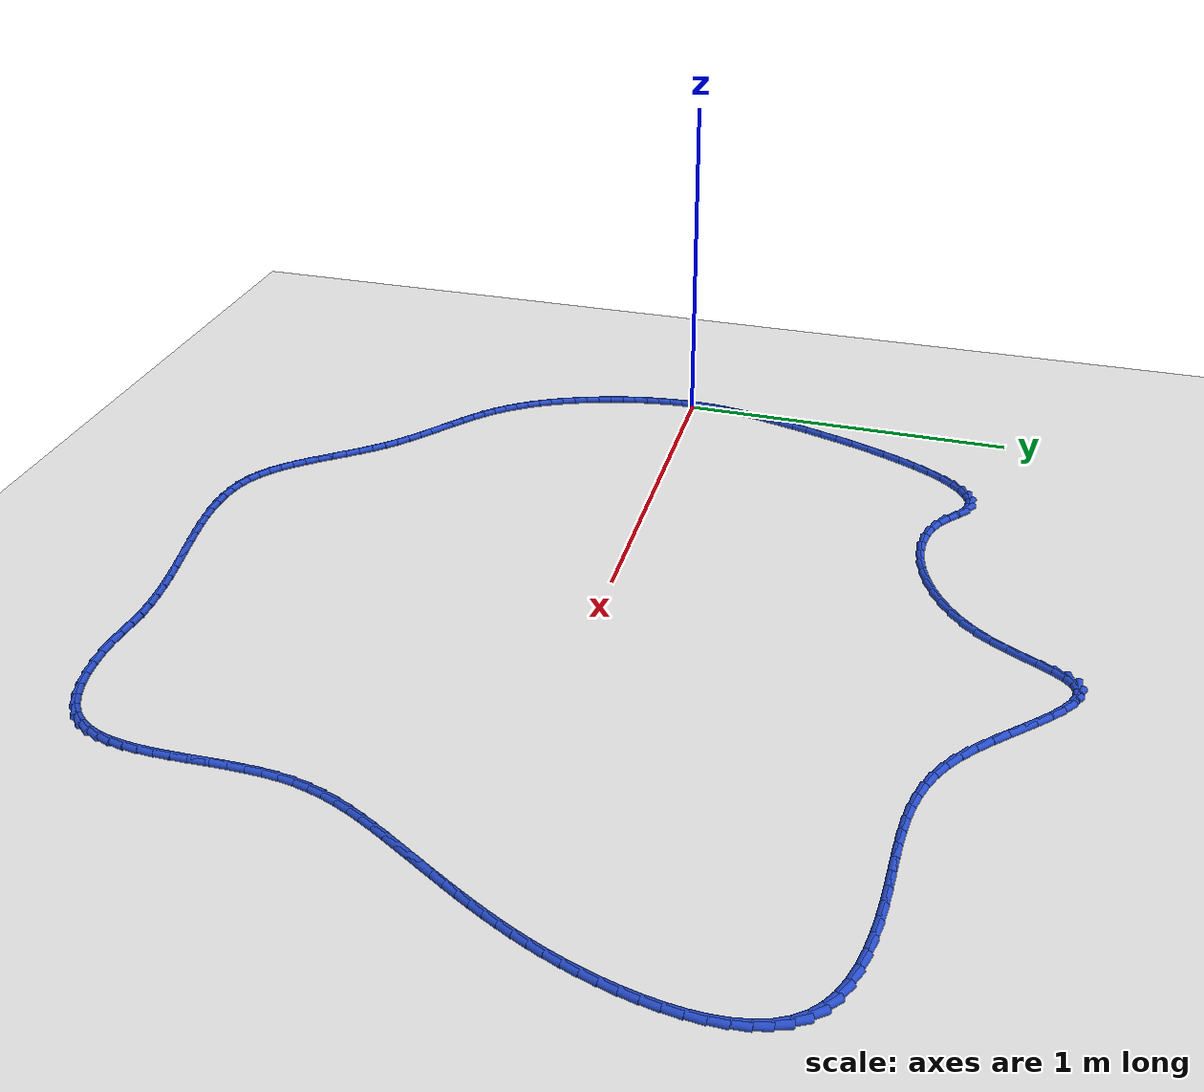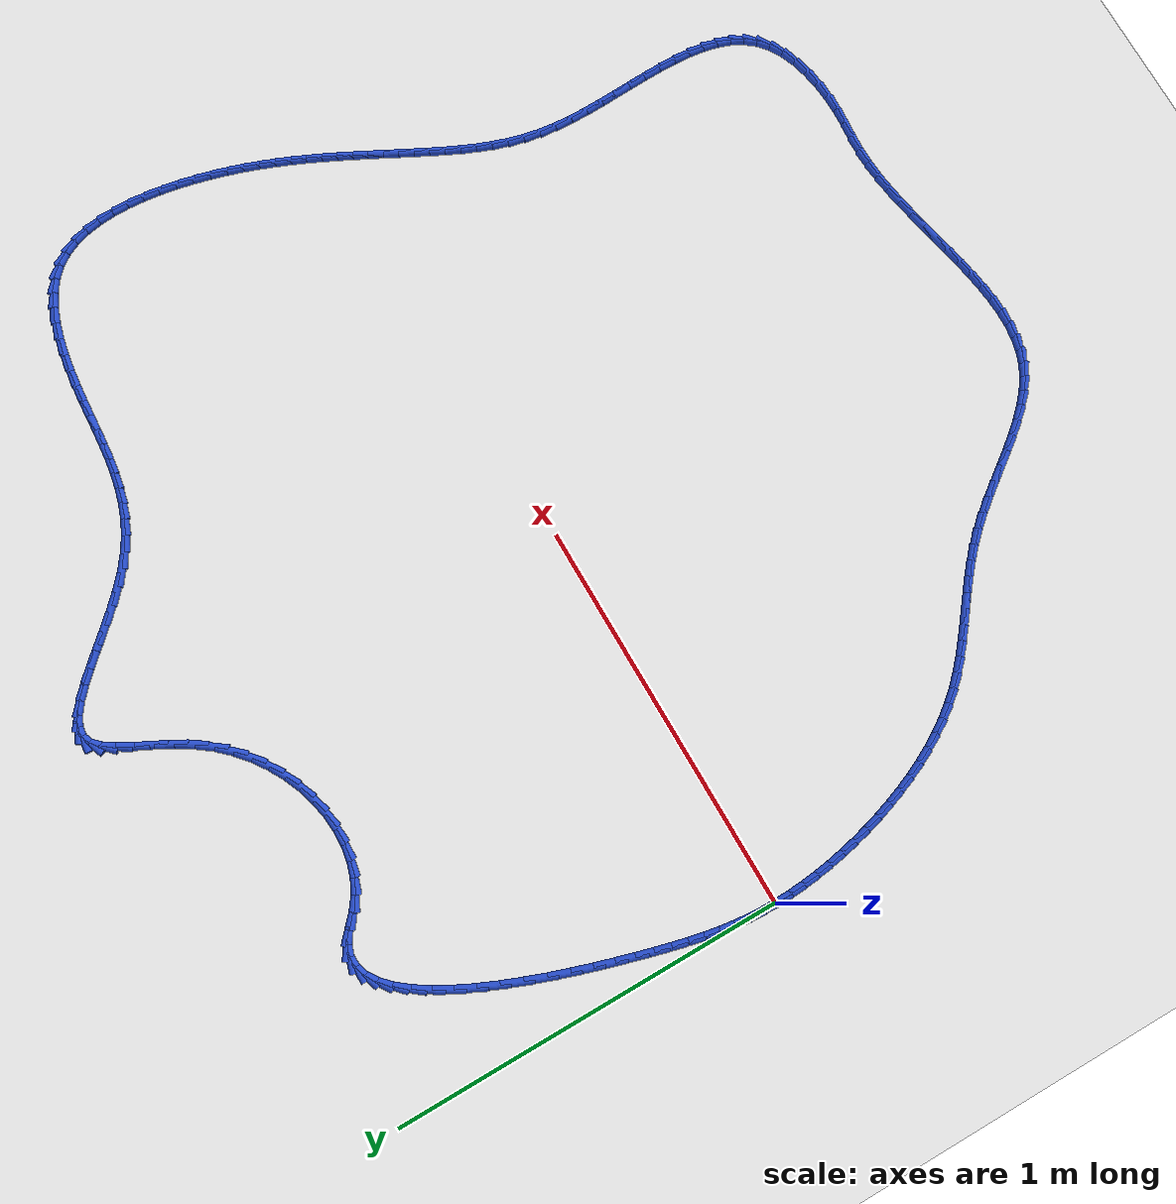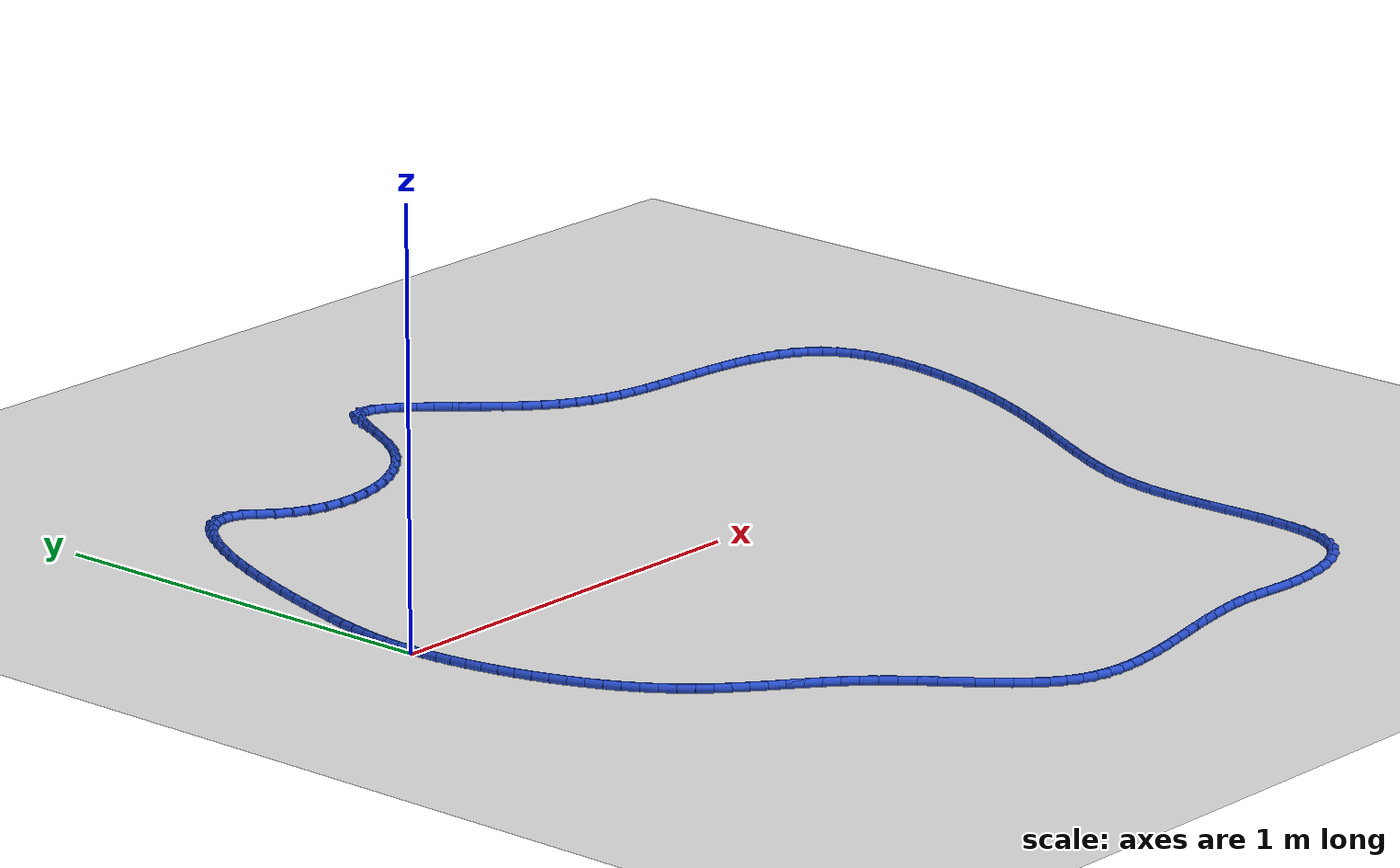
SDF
<sdf version="1.6">
 <world name="default">
  <light name="sun" type="directional">
   <pose>0 0 10 0 -0 0</pose>
   <diffuse>0.8 0.8 0.8 1</diffuse>
   <specular>0.2 0.2 0.2 1</specular>
   <attenuation>
    <range>1000</range>
    <constant>0.9</constant>
    <linear>0.01</linear>
    <quadratic>0.001</quadratic>
   </attenuation>
   <direction>-0.5 0.1 -0.9</direction>
  </light>
  <model name="ground_plane">
   <static>1</static>
   <link name="link">
    <collision name="collision">
     <geometry><plane><normal>0 0 1</normal><size>100 100</size></plane></geometry>
     <surface><friction><ode><mu>100</mu><mu2>50</mu2></ode></friction></surface>
    </collision>
    <visual name="visual">
     <cast_shadows>0</cast_shadows>
     <geometry><plane><normal>0 0 1</normal><size>100 100</size></plane></geometry>
     <material>
      <script><uri>file://media/materials/scripts/gazebo.material</uri><name>Gazebo/WhiteGlow</name></script>
     </material>
    </visual>
   </link>
  </model>
  <gravity>0 0 -9.8</gravity>
  <magnetic_field>6e-06 2.3e-05 -4.2e-05</magnetic_field>
  <atmosphere type="adiabatic"/>
  <physics name="default_physics" default="0" type="ode">
   <max_step_size>0.001</max_step_size>
   <real_time_factor>1</real_time_factor>
   <real_time_update_rate>1000</real_time_update_rate>
  </physics>
  <scene><ambient>0.4 0.4 0.4 1</ambient><background>0.7 0.7 0.7 1</background><shadows>1</shadows></scene>
  <spherical_coordinates>
   <surface_model>EARTH_WGS84</surface_model>
   <latitude_deg>0</latitude_deg>
   <longitude_deg>0</longitude_deg>
   <elevation>0</elevation>
   <heading_deg>0</heading_deg>
  </spherical_coordinates>
  <model name="line">
   <link name="link_0">
    <pose>-1.8214596497756474e-17 2.7755575615628914e-17 0.01 0 1.57 1.5525167336154178</pose>
    <collision name="collision">
     <geometry><cylinder><radius>0.01</radius><length>0.08</length></cylinder></geometry>
    </collision>
    <visual name="visual">
     <material>
      <script><name>Gazebo/Blue</name><uri>file://media/materials/scripts/gazebo.material</uri></script>
     </material>
     <geometry><cylinder><radius>0.01</radius><length>0.08</length></cylinder></geometry>
    </visual>
   </link>
   <link name="link_1">
    <pose>0.000661402451939472 0.0361785284837836 0.01 0 1.57 1.5084615165804935</pose>
    <collision name="collision">
     <geometry><cylinder><radius>0.01</radius><length>0.08</length></cylinder></geometry>
    </collision>
    <visual name="visual">
     <material>
      <script><name>Gazebo/Blue</name><uri>file://media/materials/scripts/gazebo.material</uri></script>
     </material>
     <geometry><cylinder><radius>0.01</radius><length>0.08</length></cylinder></geometry>
    </visual>
   </link>
   <link name="link_2">
    <pose>0.0028927464432620766 0.07192826730148752 0.01 0 1.57 1.4653621089082032</pose>
    <collision name="collision">
     <geometry><cylinder><radius>0.01</radius><length>0.08</length></cylinder></geometry>
    </collision>
    <visual name="visual">
     <material>
      <script><name>Gazebo/Blue</name><uri>file://media/materials/scripts/gazebo.material</uri></script>
     </material>
     <geometry><cylinder><radius>0.01</radius><length>0.08</length></cylinder></geometry>
    </visual>
   </link>
   <link name="link_3">
    <pose>0.0066811780624508234 0.10772673392677257 0.01 0 1.57 1.4250320973328217</pose>
    <collision name="collision">
     <geometry><cylinder><radius>0.01</radius><length>0.08</length></cylinder></geometry>
    </collision>
    <visual name="visual">
     <material>
      <script><name>Gazebo/Blue</name><uri>file://media/materials/scripts/gazebo.material</uri></script>
     </material>
     <geometry><cylinder><radius>0.01</radius><length>0.08</length></cylinder></geometry>
    </visual>
   </link>
   <link name="link_4">
    <pose>0.012013843397988735 0.14405144583329935 0.01 0 1.57 1.388945505339191</pose>
    <collision name="collision">
     <geometry><cylinder><radius>0.01</radius><length>0.08</length></cylinder></geometry>
    </collision>
    <visual name="visual">
     <material>
      <script><name>Gazebo/Blue</name><uri>file://media/materials/scripts/gazebo.material</uri></script>
     </material>
     <geometry><cylinder><radius>0.01</radius><length>0.08</length></cylinder></geometry>
    </visual>
   </link>
   <link name="link_5">
    <pose>0.018877888538358832 0.18137992049472856 0.01 0 1.57 1.3580728183663326</pose>
    <collision name="collision">
     <geometry><cylinder><radius>0.01</radius><length>0.08</length></cylinder></geometry>
    </collision>
    <visual name="visual">
     <material>
      <script><name>Gazebo/Blue</name><uri>file://media/materials/scripts/gazebo.material</uri></script>
     </material>
     <geometry><cylinder><radius>0.01</radius><length>0.08</length></cylinder></geometry>
    </visual>
   </link>
   <link name="link_6">
    <pose>0.027260459572044142 0.220189675384721 0.01 0 1.57 1.3328455503188137</pose>
    <collision name="collision">
     <geometry><cylinder><radius>0.01</radius><length>0.08</length></cylinder></geometry>
    </collision>
    <visual name="visual">
     <material>
      <script><name>Gazebo/Blue</name><uri>file://media/materials/scripts/gazebo.material</uri></script>
     </material>
     <geometry><cylinder><radius>0.01</radius><length>0.08</length></cylinder></geometry>
    </visual>
   </link>
   <link name="link_7">
    <pose>0.03714870258752768 0.26095822797693724 0.01 0 1.57 1.3132267445108643</pose>
    <collision name="collision">
     <geometry><cylinder><radius>0.01</radius><length>0.08</length></cylinder></geometry>
    </collision>
    <visual name="visual">
     <material>
      <script><name>Gazebo/Blue</name><uri>file://media/materials/scripts/gazebo.material</uri></script>
     </material>
     <geometry><cylinder><radius>0.01</radius><length>0.08</length></cylinder></geometry>
    </visual>
   </link>
   <link name="link_8">
    <pose>0.04852976367329247 0.30416309574503797 0.01 0 1.57 1.298671600332839</pose>
    <collision name="collision">
     <geometry><cylinder><radius>0.01</radius><length>0.08</length></cylinder></geometry>
    </collision>
    <visual name="visual">
     <material>
      <script><name>Gazebo/Blue</name><uri>file://media/materials/scripts/gazebo.material</uri></script>
     </material>
     <geometry><cylinder><radius>0.01</radius><length>0.08</length></cylinder></geometry>
    </visual>
   </link>
   <link name="link_9">
    <pose>0.061389250148750296 0.35024668932478076 0.01 0 1.57 1.2855595644924356</pose>
    <collision name="collision">
     <geometry><cylinder><radius>0.01</radius><length>0.08</length></cylinder></geometry>
    </collision>
    <visual name="visual">
     <material>
      <script><name>Gazebo/Blue</name><uri>file://media/materials/scripts/gazebo.material</uri></script>
     </material>
     <geometry><cylinder><radius>0.01</radius><length>0.08</length></cylinder></geometry>
    </visual>
   </link>
   <link name="link_10">
    <pose>0.07568402391180018 0.3989955958938321 0.01 0 1.57 1.2707426323777362</pose>
    <collision name="collision">
     <geometry><cylinder><radius>0.01</radius><length>0.08</length></cylinder></geometry>
    </collision>
    <visual name="visual">
     <material>
      <script><name>Gazebo/Blue</name><uri>file://media/materials/scripts/gazebo.material</uri></script>
     </material>
     <geometry><cylinder><radius>0.01</radius><length>0.08</length></cylinder></geometry>
    </visual>
   </link>
   <link name="link_11">
    <pose>0.09134547076444016 0.4496151684564415 0.01 0 1.57 1.2536949764877952</pose>
    <collision name="collision">
     <geometry><cylinder><radius>0.01</radius><length>0.08</length></cylinder></geometry>
    </collision>
    <visual name="visual">
     <material>
      <script><name>Gazebo/Blue</name><uri>file://media/materials/scripts/gazebo.material</uri></script>
     </material>
     <geometry><cylinder><radius>0.01</radius><length>0.08</length></cylinder></geometry>
    </visual>
   </link>
   <link name="link_12">
    <pose>0.10830409459419382 0.5012906392404055 0.01 0 1.57 1.233855656656442</pose>
    <collision name="collision">
     <geometry><cylinder><radius>0.01</radius><length>0.08</length></cylinder></geometry>
    </collision>
    <visual name="visual">
     <material>
      <script><name>Gazebo/Blue</name><uri>file://media/materials/scripts/gazebo.material</uri></script>
     </material>
     <geometry><cylinder><radius>0.01</radius><length>0.08</length></cylinder></geometry>
    </visual>
   </link>
   <link name="link_13">
    <pose>0.12649039928858483 0.55320724047352 0.01 0 1.57 1.2104747634968034</pose>
    <collision name="collision">
     <geometry><cylinder><radius>0.01</radius><length>0.08</length></cylinder></geometry>
    </collision>
    <visual name="visual">
     <material>
      <script><name>Gazebo/Blue</name><uri>file://media/materials/scripts/gazebo.material</uri></script>
     </material>
     <geometry><cylinder><radius>0.01</radius><length>0.08</length></cylinder></geometry>
    </visual>
   </link>
   <link name="link_14">
    <pose>0.14583488873513678 0.6045502043835819 0.01 0 1.57 1.1825252440488485</pose>
    <collision name="collision">
     <geometry><cylinder><radius>0.01</radius><length>0.08</length></cylinder></geometry>
    </collision>
    <visual name="visual">
     <material>
      <script><name>Gazebo/Blue</name><uri>file://media/materials/scripts/gazebo.material</uri></script>
     </material>
     <geometry><cylinder><radius>0.01</radius><length>0.08</length></cylinder></geometry>
    </visual>
   </link>
   <link name="link_15">
    <pose>0.1662680668213734 0.6545047631983871 0.01 0 1.57 1.1485652225012108</pose>
    <collision name="collision">
     <geometry><cylinder><radius>0.01</radius><length>0.08</length></cylinder></geometry>
    </collision>
    <visual name="visual">
     <material>
      <script><name>Gazebo/Blue</name><uri>file://media/materials/scripts/gazebo.material</uri></script>
     </material>
     <geometry><cylinder><radius>0.01</radius><length>0.08</length></cylinder></geometry>
    </visual>
   </link>
   <link name="link_16">
    <pose>0.1877204374348183 0.7022561491457324 0.01 0 1.57 1.1065168290132088</pose>
    <collision name="collision">
     <geometry><cylinder><radius>0.01</radius><length>0.08</length></cylinder></geometry>
    </collision>
    <visual name="visual">
     <material>
      <script><name>Gazebo/Blue</name><uri>file://media/materials/scripts/gazebo.material</uri></script>
     </material>
     <geometry><cylinder><radius>0.01</radius><length>0.08</length></cylinder></geometry>
    </visual>
   </link>
   <link name="link_17">
    <pose>0.21012250446299505 0.7469895944534137 0.01 0 1.57 1.0533028723605897</pose>
    <collision name="collision">
     <geometry><cylinder><radius>0.01</radius><length>0.08</length></cylinder></geometry>
    </collision>
    <visual name="visual">
     <material>
      <script><name>Gazebo/Blue</name><uri>file://media/materials/scripts/gazebo.material</uri></script>
     </material>
     <geometry><cylinder><radius>0.01</radius><length>0.08</length></cylinder></geometry>
    </visual>
   </link>
   <link name="link_18">
    <pose>0.23340477179342742 0.7878903313492277 0.01 0 1.57 0.9842439488143678</pose>
    <collision name="collision">
     <geometry><cylinder><radius>0.01</radius><length>0.08</length></cylinder></geometry>
    </collision>
    <visual name="visual">
     <material>
      <script><name>Gazebo/Blue</name><uri>file://media/materials/scripts/gazebo.material</uri></script>
     </material>
     <geometry><cylinder><radius>0.01</radius><length>0.08</length></cylinder></geometry>
    </visual>
   </link>
   <link name="link_19">
    <pose>0.25749774331363895 0.8241435920609707 0.01 0 1.57 0.8920804210931597</pose>
    <collision name="collision">
     <geometry><cylinder><radius>0.01</radius><length>0.08</length></cylinder></geometry>
    </collision>
    <visual name="visual">
     <material>
      <script><name>Gazebo/Blue</name><uri>file://media/materials/scripts/gazebo.material</uri></script>
     </material>
     <geometry><cylinder><radius>0.01</radius><length>0.08</length></cylinder></geometry>
    </visual>
   </link>
   <link name="link_20">
    <pose>0.28233192291115317 0.8549346088164385 0.01 0 1.57 0.7655709221809681</pose>
    <collision name="collision">
     <geometry><cylinder><radius>0.01</radius><length>0.08</length></cylinder></geometry>
    </collision>
    <visual name="visual">
     <material>
      <script><name>Gazebo/Blue</name><uri>file://media/materials/scripts/gazebo.material</uri></script>
     </material>
     <geometry><cylinder><radius>0.01</radius><length>0.08</length></cylinder></geometry>
    </visual>
   </link>
   <link name="link_21">
    <pose>0.307837814473494 0.8794486138434283 0.01 0 1.57 0.5884485016935522</pose>
    <collision name="collision">
     <geometry><cylinder><radius>0.01</radius><length>0.08</length></cylinder></geometry>
    </collision>
    <visual name="visual">
     <material>
      <script><name>Gazebo/Blue</name><uri>file://media/materials/scripts/gazebo.material</uri></script>
     </material>
     <geometry><cylinder><radius>0.01</radius><length>0.08</length></cylinder></geometry>
    </visual>
   </link>
   <link name="link_22">
    <pose>0.33394592188818484 0.8968708393697358 0.01 0 1.57 0.34306046348840885</pose>
    <collision name="collision">
     <geometry><cylinder><radius>0.01</radius><length>0.08</length></cylinder></geometry>
    </collision>
    <visual name="visual">
     <material>
      <script><name>Gazebo/Blue</name><uri>file://media/materials/scripts/gazebo.material</uri></script>
     </material>
     <geometry><cylinder><radius>0.01</radius><length>0.08</length></cylinder></geometry>
    </visual>
   </link>
   <link name="link_23">
    <pose>0.36058674904274945 0.9063865176231579 0.01 0 1.57 0.02929952763949501</pose>
    <collision name="collision">
     <geometry><cylinder><radius>0.01</radius><length>0.08</length></cylinder></geometry>
    </collision>
    <visual name="visual">
     <material>
      <script><name>Gazebo/Blue</name><uri>file://media/materials/scripts/gazebo.material</uri></script>
     </material>
     <geometry><cylinder><radius>0.01</radius><length>0.08</length></cylinder></geometry>
    </visual>
   </link>
   <link name="link_24">
    <pose>0.38769079982471155 0.9071808808314907 0.01 0 1.57 -0.30780265959698605</pose>
    <collision name="collision">
     <geometry><cylinder><radius>0.01</radius><length>0.08</length></cylinder></geometry>
    </collision>
    <visual name="visual">
     <material>
      <script><name>Gazebo/Blue</name><uri>file://media/materials/scripts/gazebo.material</uri></script>
     </material>
     <geometry><cylinder><radius>0.01</radius><length>0.08</length></cylinder></geometry>
    </visual>
   </link>
   <link name="link_25">
    <pose>0.4151885781215945 0.8984391612225302 0.01 0 1.57 -0.601246775000382</pose>
    <collision name="collision">
     <geometry><cylinder><radius>0.01</radius><length>0.08</length></cylinder></geometry>
    </collision>
    <visual name="visual">
     <material>
      <script><name>Gazebo/Blue</name><uri>file://media/materials/scripts/gazebo.material</uri></script>
     </material>
     <geometry><cylinder><radius>0.01</radius><length>0.08</length></cylinder></geometry>
    </visual>
   </link>
   <link name="link_26">
    <pose>0.4430119001629754 0.8793532334128125 0.01 0 1.57 -0.7452722203826176</pose>
    <collision name="collision">
     <geometry><cylinder><radius>0.01</radius><length>0.08</length></cylinder></geometry>
    </collision>
    <visual name="visual">
     <material>
      <script><name>Gazebo/Blue</name><uri>file://media/materials/scripts/gazebo.material</uri></script>
     </material>
     <geometry><cylinder><radius>0.01</radius><length>0.08</length></cylinder></geometry>
    </visual>
   </link>
   <link name="link_27">
    <pose>0.47181535726868373 0.8527732813059352 0.01 0 1.57 -0.6346864906345117</pose>
    <collision name="collision">
     <geometry><cylinder><radius>0.01</radius><length>0.08</length></cylinder></geometry>
    </collision>
    <visual name="visual">
     <material>
      <script><name>Gazebo/Blue</name><uri>file://media/materials/scripts/gazebo.material</uri></script>
     </material>
     <geometry><cylinder><radius>0.01</radius><length>0.08</length></cylinder></geometry>
    </visual>
   </link>
   <link name="link_28">
    <pose>0.5036969247259705 0.8292983328843618 0.01 0 1.57 -0.4669300043281286</pose>
    <collision name="collision">
     <geometry><cylinder><radius>0.01</radius><length>0.08</length></cylinder></geometry>
    </collision>
    <visual name="visual">
     <material>
      <script><name>Gazebo/Blue</name><uri>file://media/materials/scripts/gazebo.material</uri></script>
     </material>
     <geometry><cylinder><radius>0.01</radius><length>0.08</length></cylinder></geometry>
    </visual>
   </link>
   <link name="link_29">
    <pose>0.5387693777937349 0.8116179672019037 0.01 0 1.57 -0.30972719676801136</pose>
    <collision name="collision">
     <geometry><cylinder><radius>0.01</radius><length>0.08</length></cylinder></geometry>
    </collision>
    <visual name="visual">
     <material>
      <script><name>Gazebo/Blue</name><uri>file://media/materials/scripts/gazebo.material</uri></script>
     </material>
     <geometry><cylinder><radius>0.01</radius><length>0.08</length></cylinder></geometry>
    </visual>
   </link>
   <link name="link_30">
    <pose>0.576452486745119 0.7995583648470999 0.01 0 1.57 -0.16501000302837293</pose>
    <collision name="collision">
     <geometry><cylinder><radius>0.01</radius><length>0.08</length></cylinder></geometry>
    </collision>
    <visual name="visual">
     <material>
      <script><name>Gazebo/Blue</name><uri>file://media/materials/scripts/gazebo.material</uri></script>
     </material>
     <geometry><cylinder><radius>0.01</radius><length>0.08</length></cylinder></geometry>
    </visual>
   </link>
   <link name="link_31">
    <pose>0.616165881339732 0.7929451258264658 0.01 0 1.57 -0.03257272774613214</pose>
    <collision name="collision">
     <geometry><cylinder><radius>0.01</radius><length>0.08</length></cylinder></geometry>
    </collision>
    <visual name="visual">
     <material>
      <script><name>Gazebo/Blue</name><uri>file://media/materials/scripts/gazebo.material</uri></script>
     </material>
     <geometry><cylinder><radius>0.01</radius><length>0.08</length></cylinder></geometry>
    </visual>
   </link>
   <link name="link_32">
    <pose>0.6573291913371824 0.7916038501465174 0.01 0 1.57 0.08912874974139268</pose>
    <collision name="collision">
     <geometry><cylinder><radius>0.01</radius><length>0.08</length></cylinder></geometry>
    </collision>
    <visual name="visual">
     <material>
      <script><name>Gazebo/Blue</name><uri>file://media/materials/scripts/gazebo.material</uri></script>
     </material>
     <geometry><cylinder><radius>0.01</radius><length>0.08</length></cylinder></geometry>
    </visual>
   </link>
   <link name="link_33">
    <pose>0.6993620464970786 0.7953601378137694 0.01 0 1.57 0.2022764824054154</pose>
    <collision name="collision">
     <geometry><cylinder><radius>0.01</radius><length>0.08</length></cylinder></geometry>
    </collision>
    <visual name="visual">
     <material>
      <script><name>Gazebo/Blue</name><uri>file://media/materials/scripts/gazebo.material</uri></script>
     </material>
     <geometry><cylinder><radius>0.01</radius><length>0.08</length></cylinder></geometry>
    </visual>
   </link>
   <link name="link_34">
    <pose>0.74168407657903 0.8040395888347384 0.01 0 1.57 0.30923556400715935</pose>
    <collision name="collision">
     <geometry><cylinder><radius>0.01</radius><length>0.08</length></cylinder></geometry>
    </collision>
    <visual name="visual">
     <material>
      <script><name>Gazebo/Blue</name><uri>file://media/materials/scripts/gazebo.material</uri></script>
     </material>
     <geometry><cylinder><radius>0.01</radius><length>0.08</length></cylinder></geometry>
    </visual>
   </link>
   <link name="link_35">
    <pose>0.7837149113426448 0.8174678032159395 0.01 0 1.57 0.412316580234775</pose>
    <collision name="collision">
     <geometry><cylinder><radius>0.01</radius><length>0.08</length></cylinder></geometry>
    </collision>
    <visual name="visual">
     <material>
      <script><name>Gazebo/Blue</name><uri>file://media/materials/scripts/gazebo.material</uri></script>
     </material>
     <geometry><cylinder><radius>0.01</radius><length>0.08</length></cylinder></geometry>
    </visual>
   </link>
   <link name="link_36">
    <pose>0.8248741805475321 0.8354703809638884 0.01 0 1.57 0.5136734907480246</pose>
    <collision name="collision">
     <geometry><cylinder><radius>0.01</radius><length>0.08</length></cylinder></geometry>
    </collision>
    <visual name="visual">
     <material>
      <script><name>Gazebo/Blue</name><uri>file://media/materials/scripts/gazebo.material</uri></script>
     </material>
     <geometry><cylinder><radius>0.01</radius><length>0.08</length></cylinder></geometry>
    </visual>
   </link>
   <link name="link_37">
    <pose>0.8645815139533001 0.8578729220851005 0.01 0 1.57 0.6152644523403845</pose>
    <collision name="collision">
     <geometry><cylinder><radius>0.01</radius><length>0.08</length></cylinder></geometry>
    </collision>
    <visual name="visual">
     <material>
      <script><name>Gazebo/Blue</name><uri>file://media/materials/scripts/gazebo.material</uri></script>
     </material>
     <geometry><cylinder><radius>0.01</radius><length>0.08</length></cylinder></geometry>
    </visual>
   </link>
   <link name="link_38">
    <pose>0.9022565413195576 0.8845010265860915 0.01 0 1.57 0.7188253262465767</pose>
    <collision name="collision">
     <geometry><cylinder><radius>0.01</radius><length>0.08</length></cylinder></geometry>
    </collision>
    <visual name="visual">
     <material>
      <script><name>Gazebo/Blue</name><uri>file://media/materials/scripts/gazebo.material</uri></script>
     </material>
     <geometry><cylinder><radius>0.01</radius><length>0.08</length></cylinder></geometry>
    </visual>
   </link>
   <link name="link_39">
    <pose>0.9373188924059142 0.9151802944733775 0.01 0 1.57 0.8258234464255539</pose>
    <collision name="collision">
     <geometry><cylinder><radius>0.01</radius><length>0.08</length></cylinder></geometry>
    </collision>
    <visual name="visual">
     <material>
      <script><name>Gazebo/Blue</name><uri>file://media/materials/scripts/gazebo.material</uri></script>
     </material>
     <geometry><cylinder><radius>0.01</radius><length>0.08</length></cylinder></geometry>
    </visual>
   </link>
   <link name="link_40">
    <pose>0.9691881969719773 0.9497363257534732 0.01 0 1.57 0.9364915513400681</pose>
    <collision name="collision">
     <geometry><cylinder><radius>0.01</radius><length>0.08</length></cylinder></geometry>
    </collision>
    <visual name="visual">
     <material>
      <script><name>Gazebo/Blue</name><uri>file://media/materials/scripts/gazebo.material</uri></script>
     </material>
     <geometry><cylinder><radius>0.01</radius><length>0.08</length></cylinder></geometry>
    </visual>
   </link>
   <link name="link_41">
    <pose>0.9973096342947964 0.9879588866808945 0.01 0 1.57 1.0291346631655864</pose>
    <collision name="collision">
     <geometry><cylinder><radius>0.01</radius><length>0.08</length></cylinder></geometry>
    </collision>
    <visual name="visual">
     <material>
      <script><name>Gazebo/Blue</name><uri>file://media/materials/scripts/gazebo.material</uri></script>
     </material>
     <geometry><cylinder><radius>0.01</radius><length>0.08</length></cylinder></geometry>
    </visual>
   </link>
   <link name="link_42">
    <pose>1.021811196163584 1.0286800841617525 0.01 0 1.57 1.083195679463618</pose>
    <collision name="collision">
     <geometry><cylinder><radius>0.01</radius><length>0.08</length></cylinder></geometry>
    </collision>
    <visual name="visual">
     <material>
      <script><name>Gazebo/Blue</name><uri>file://media/materials/scripts/gazebo.material</uri></script>
     </material>
     <geometry><cylinder><radius>0.01</radius><length>0.08</length></cylinder></geometry>
    </visual>
   </link>
   <link name="link_43">
    <pose>1.0435611611834594 1.069693756796988 0.01 0 1.57 1.0993995483852652</pose>
    <collision name="collision">
     <geometry><cylinder><radius>0.01</radius><length>0.08</length></cylinder></geometry>
    </collision>
    <visual name="visual">
     <material>
      <script><name>Gazebo/Blue</name><uri>file://media/materials/scripts/gazebo.material</uri></script>
     </material>
     <geometry><cylinder><radius>0.01</radius><length>0.08</length></cylinder></geometry>
    </visual>
   </link>
   <link name="link_44">
    <pose>1.0634648758783545 1.1087417546279525 0.01 0 1.57 1.0721623427009501</pose>
    <collision name="collision">
     <geometry><cylinder><radius>0.01</radius><length>0.08</length></cylinder></geometry>
    </collision>
    <visual name="visual">
     <material>
      <script><name>Gazebo/Blue</name><uri>file://media/materials/scripts/gazebo.material</uri></script>
     </material>
     <geometry><cylinder><radius>0.01</radius><length>0.08</length></cylinder></geometry>
    </visual>
   </link>
   <link name="link_45">
    <pose>1.0824276867722027 1.1435659276959964 0.01 0 1.57 0.982001378980577</pose>
    <collision name="collision">
     <geometry><cylinder><radius>0.01</radius><length>0.08</length></cylinder></geometry>
    </collision>
    <visual name="visual">
     <material>
      <script><name>Gazebo/Blue</name><uri>file://media/materials/scripts/gazebo.material</uri></script>
     </material>
     <geometry><cylinder><radius>0.01</radius><length>0.08</length></cylinder></geometry>
    </visual>
   </link>
   <link name="link_46">
    <pose>1.1013549403889367 1.1719081260424706 0.01 0 1.57 0.7804496360444808</pose>
    <collision name="collision">
     <geometry><cylinder><radius>0.01</radius><length>0.08</length></cylinder></geometry>
    </collision>
    <visual name="visual">
     <material>
      <script><name>Gazebo/Blue</name><uri>file://media/materials/scripts/gazebo.material</uri></script>
     </material>
     <geometry><cylinder><radius>0.01</radius><length>0.08</length></cylinder></geometry>
    </visual>
   </link>
   <link name="link_47">
    <pose>1.121151983252489 1.1915101997087263 0.01 0 1.57 0.3834261873655466</pose>
    <collision name="collision">
     <geometry><cylinder><radius>0.01</radius><length>0.08</length></cylinder></geometry>
    </collision>
    <visual name="visual">
     <material>
      <script><name>Gazebo/Blue</name><uri>file://media/materials/scripts/gazebo.material</uri></script>
     </material>
     <geometry><cylinder><radius>0.01</radius><length>0.08</length></cylinder></geometry>
    </visual>
   </link>
   <link name="link_48">
    <pose>1.1426994661061665 1.2002022592850703 0.01 0 1.57 -0.10505992513715576</pose>
    <collision name="collision">
     <geometry><cylinder><radius>0.01</radius><length>0.08</length></cylinder></geometry>
    </collision>
    <visual name="visual">
     <material>
      <script><name>Gazebo/Blue</name><uri>file://media/materials/scripts/gazebo.material</uri></script>
     </material>
     <geometry><cylinder><radius>0.01</radius><length>0.08</length></cylinder></geometry>
    </visual>
   </link>
   <link name="link_49">
    <pose>1.1663480478872639 1.1977085594850374 0.01 0 1.57 -0.44274785096787167</pose>
    <collision name="collision">
     <geometry><cylinder><radius>0.01</radius><length>0.08</length></cylinder></geometry>
    </collision>
    <visual name="visual">
     <material>
      <script><name>Gazebo/Blue</name><uri>file://media/materials/scripts/gazebo.material</uri></script>
     </material>
     <geometry><cylinder><radius>0.01</radius><length>0.08</length></cylinder></geometry>
    </visual>
   </link>
   <link name="link_50">
    <pose>1.1919386905236564 1.1855749673264873 0.01 0 1.57 -0.6350031741727635</pose>
    <collision name="collision">
     <geometry><cylinder><radius>0.01</radius><length>0.08</length></cylinder></geometry>
    </collision>
    <visual name="visual">
     <material>
      <script><name>Gazebo/Blue</name><uri>file://media/materials/scripts/gazebo.material</uri></script>
     </material>
     <geometry><cylinder><radius>0.01</radius><length>0.08</length></cylinder></geometry>
    </visual>
   </link>
   <link name="link_51">
    <pose>1.2192917210618186 1.1654210970793921 0.01 0 1.57 -0.7425122486347941</pose>
    <collision name="collision">
     <geometry><cylinder><radius>0.01</radius><length>0.08</length></cylinder></geometry>
    </collision>
    <visual name="visual">
     <material>
      <script><name>Gazebo/Blue</name><uri>file://media/materials/scripts/gazebo.material</uri></script>
     </material>
     <geometry><cylinder><radius>0.01</radius><length>0.08</length></cylinder></geometry>
    </visual>
   </link>
   <link name="link_52">
    <pose>1.2482274665482247 1.1388665630137256 0.01 0 1.57 -0.8015589986895567</pose>
    <collision name="collision">
     <geometry><cylinder><radius>0.01</radius><length>0.08</length></cylinder></geometry>
    </collision>
    <visual name="visual">
     <material>
      <script><name>Gazebo/Blue</name><uri>file://media/materials/scripts/gazebo.material</uri></script>
     </material>
     <geometry><cylinder><radius>0.01</radius><length>0.08</length></cylinder></geometry>
    </visual>
   </link>
   <link name="link_53">
    <pose>1.2785662540293492 1.1075309793994614 0.01 0 1.57 -0.8297967448984692</pose>
    <collision name="collision">
     <geometry><cylinder><radius>0.01</radius><length>0.08</length></cylinder></geometry>
    </collision>
    <visual name="visual">
     <material>
      <script><name>Gazebo/Blue</name><uri>file://media/materials/scripts/gazebo.material</uri></script>
     </material>
     <geometry><cylinder><radius>0.01</radius><length>0.08</length></cylinder></geometry>
    </visual>
   </link>
   <link name="link_54">
    <pose>1.3101284105516677 1.0730339605065715 0.01 0 1.57 -0.8353674964339666</pose>
    <collision name="collision">
     <geometry><cylinder><radius>0.01</radius><length>0.08</length></cylinder></geometry>
    </collision>
    <visual name="visual">
     <material>
      <script><name>Gazebo/Blue</name><uri>file://media/materials/scripts/gazebo.material</uri></script>
     </material>
     <geometry><cylinder><radius>0.01</radius><length>0.08</length></cylinder></geometry>
    </visual>
   </link>
   <link name="link_55">
    <pose>1.3427342631616543 1.0369951206050294 0.01 0 1.57 -0.8212626258218181</pose>
    <collision name="collision">
     <geometry><cylinder><radius>0.01</radius><length>0.08</length></cylinder></geometry>
    </collision>
    <visual name="visual">
     <material>
      <script><name>Gazebo/Blue</name><uri>file://media/materials/scripts/gazebo.material</uri></script>
     </material>
     <geometry><cylinder><radius>0.01</radius><length>0.08</length></cylinder></geometry>
    </visual>
   </link>
   <link name="link_56">
    <pose>1.3762041389057833 1.001034073964809 0.01 0 1.57 -0.7869973523059962</pose>
    <collision name="collision">
     <geometry><cylinder><radius>0.01</radius><length>0.08</length></cylinder></geometry>
    </collision>
    <visual name="visual">
     <material>
      <script><name>Gazebo/Blue</name><uri>file://media/materials/scripts/gazebo.material</uri></script>
     </material>
     <geometry><cylinder><radius>0.01</radius><length>0.08</length></cylinder></geometry>
    </visual>
   </link>
   <link name="link_57">
    <pose>1.4103583648305305 0.9667704348558821 0.01 0 1.57 -0.728873478555405</pose>
    <collision name="collision">
     <geometry><cylinder><radius>0.01</radius><length>0.08</length></cylinder></geometry>
    </collision>
    <visual name="visual">
     <material>
      <script><name>Gazebo/Blue</name><uri>file://media/materials/scripts/gazebo.material</uri></script>
     </material>
     <geometry><cylinder><radius>0.01</radius><length>0.08</length></cylinder></geometry>
    </visual>
   </link>
   <link name="link_58">
    <pose>1.4450172679823694 0.9358238175482223 0.01 0 1.57 -0.6425276906787861</pose>
    <collision name="collision">
     <geometry><cylinder><radius>0.01</radius><length>0.08</length></cylinder></geometry>
    </collision>
    <visual name="visual">
     <material>
      <script><name>Gazebo/Blue</name><uri>file://media/materials/scripts/gazebo.material</uri></script>
     </material>
     <geometry><cylinder><radius>0.01</radius><length>0.08</length></cylinder></geometry>
    </visual>
   </link>
   <link name="link_59">
    <pose>1.4800213082218185 0.9096239884934376 0.01 0 1.57 -0.5444921097442679</pose>
    <collision name="collision">
     <geometry><cylinder><radius>0.01</radius><length>0.08</length></cylinder></geometry>
    </collision>
    <visual name="visual">
     <material>
      <script><name>Gazebo/Blue</name><uri>file://media/materials/scripts/gazebo.material</uri></script>
     </material>
     <geometry><cylinder><radius>0.01</radius><length>0.08</length></cylinder></geometry>
    </visual>
   </link>
   <link name="link_60">
    <pose>1.5153566685774595 0.888226578094227 0.01 0 1.57 -0.4475187058245623</pose>
    <collision name="collision">
     <geometry><cylinder><radius>0.01</radius><length>0.08</length></cylinder></geometry>
    </collision>
    <visual name="visual">
     <material>
      <script><name>Gazebo/Blue</name><uri>file://media/materials/scripts/gazebo.material</uri></script>
     </material>
     <geometry><cylinder><radius>0.01</radius><length>0.08</length></cylinder></geometry>
    </visual>
   </link>
   <link name="link_61">
    <pose>1.551073663035115 0.8710824765368503 0.01 0 1.57 -0.35601677669430337</pose>
    <collision name="collision">
     <geometry><cylinder><radius>0.01</radius><length>0.08</length></cylinder></geometry>
    </collision>
    <visual name="visual">
     <material>
      <script><name>Gazebo/Blue</name><uri>file://media/materials/scripts/gazebo.material</uri></script>
     </material>
     <geometry><cylinder><radius>0.01</radius><length>0.08</length></cylinder></geometry>
    </visual>
   </link>
   <link name="link_62">
    <pose>1.5872228835889723 0.8576399524524537 0.01 0 1.57 -0.2739123615513652</pose>
    <collision name="collision">
     <geometry><cylinder><radius>0.01</radius><length>0.08</length></cylinder></geometry>
    </collision>
    <visual name="visual">
     <material>
      <script><name>Gazebo/Blue</name><uri>file://media/materials/scripts/gazebo.material</uri></script>
     </material>
     <geometry><cylinder><radius>0.01</radius><length>0.08</length></cylinder></geometry>
    </visual>
   </link>
   <link name="link_63">
    <pose>1.6238549222332193 0.847347274472184 0.01 0 1.57 -0.20415111690446883</pose>
    <collision name="collision">
     <geometry><cylinder><radius>0.01</radius><length>0.08</length></cylinder></geometry>
    </collision>
    <visual name="visual">
     <material>
      <script><name>Gazebo/Blue</name><uri>file://media/materials/scripts/gazebo.material</uri></script>
     </material>
     <geometry><cylinder><radius>0.01</radius><length>0.08</length></cylinder></geometry>
    </visual>
   </link>
   <link name="link_64">
    <pose>1.6610203709620435 0.8396527112271878 0.01 0 1.57 -0.14852106244290922</pose>
    <collision name="collision">
     <geometry><cylinder><radius>0.01</radius><length>0.08</length></cylinder></geometry>
    </collision>
    <visual name="visual">
     <material>
      <script><name>Gazebo/Blue</name><uri>file://media/materials/scripts/gazebo.material</uri></script>
     </material>
     <geometry><cylinder><radius>0.01</radius><length>0.08</length></cylinder></geometry>
    </visual>
   </link>
   <link name="link_65">
    <pose>1.6987698217696332 0.8340045313486112 0.01 0 1.57 -0.10779033692860607</pose>
    <collision name="collision">
     <geometry><cylinder><radius>0.01</radius><length>0.08</length></cylinder></geometry>
    </collision>
    <visual name="visual">
     <material>
      <script><name>Gazebo/Blue</name><uri>file://media/materials/scripts/gazebo.material</uri></script>
     </material>
     <geometry><cylinder><radius>0.01</radius><length>0.08</length></cylinder></geometry>
    </visual>
   </link>
   <link name="link_66">
    <pose>1.7371538666501753 0.8298510034676012 0.01 0 1.57 -0.08199314677017787</pose>
    <collision name="collision">
     <geometry><cylinder><radius>0.01</radius><length>0.08</length></cylinder></geometry>
    </collision>
    <visual name="visual">
     <material>
      <script><name>Gazebo/Blue</name><uri>file://media/materials/scripts/gazebo.material</uri></script>
     </material>
     <geometry><cylinder><radius>0.01</radius><length>0.08</length></cylinder></geometry>
    </visual>
   </link>
   <link name="link_67">
    <pose>1.776223097597858 0.8266403962153039 0.01 0 1.57 -0.07071263654918822</pose>
    <collision name="collision">
     <geometry><cylinder><radius>0.01</radius><length>0.08</length></cylinder></geometry>
    </collision>
    <visual name="visual">
     <material>
      <script><name>Gazebo/Blue</name><uri>file://media/materials/scripts/gazebo.material</uri></script>
     </material>
     <geometry><cylinder><radius>0.01</radius><length>0.08</length></cylinder></geometry>
    </visual>
   </link>
   <link name="link_68">
    <pose>1.8160281066068684 0.823820978222866 0.01 0 1.57 -0.07328215640855079</pose>
    <collision name="collision">
     <geometry><cylinder><radius>0.01</radius><length>0.08</length></cylinder></geometry>
    </collision>
    <visual name="visual">
     <material>
      <script><name>Gazebo/Blue</name><uri>file://media/materials/scripts/gazebo.material</uri></script>
     </material>
     <geometry><cylinder><radius>0.01</radius><length>0.08</length></cylinder></geometry>
    </visual>
   </link>
   <link name="link_69">
    <pose>1.856619485671395 0.820841018121434 0.01 0 1.57 -0.08888251873500193</pose>
    <collision name="collision">
     <geometry><cylinder><radius>0.01</radius><length>0.08</length></cylinder></geometry>
    </collision>
    <visual name="visual">
     <material>
      <script><name>Gazebo/Blue</name><uri>file://media/materials/scripts/gazebo.material</uri></script>
     </material>
     <geometry><cylinder><radius>0.01</radius><length>0.08</length></cylinder></geometry>
    </visual>
   </link>
   <link name="link_70">
    <pose>1.898045246692434 0.8171492652758163 0.01 0 1.57 -0.11614829194253552</pose>
    <collision name="collision">
     <geometry><cylinder><radius>0.01</radius><length>0.08</length></cylinder></geometry>
    </collision>
    <visual name="visual">
     <material>
      <script><name>Gazebo/Blue</name><uri>file://media/materials/scripts/gazebo.material</uri></script>
     </material>
     <geometry><cylinder><radius>0.01</radius><length>0.08</length></cylinder></geometry>
    </visual>
   </link>
   <link name="link_71">
    <pose>1.9400869434991028 0.8122441166236353 0.01 0 1.57 -0.15439510878542548</pose>
    <collision name="collision">
     <geometry><cylinder><radius>0.01</radius><length>0.08</length></cylinder></geometry>
    </collision>
    <visual name="visual">
     <material>
      <script><name>Gazebo/Blue</name><uri>file://media/materials/scripts/gazebo.material</uri></script>
     </material>
     <geometry><cylinder><radius>0.01</radius><length>0.08</length></cylinder></geometry>
    </visual>
   </link>
   <link name="link_72">
    <pose>1.9820315660446006 0.8057161182945701 0.01 0 1.57 -0.20520382909856794</pose>
    <collision name="collision">
     <geometry><cylinder><radius>0.01</radius><length>0.08</length></cylinder></geometry>
    </collision>
    <visual name="visual">
     <material>
      <script><name>Gazebo/Blue</name><uri>file://media/materials/scripts/gazebo.material</uri></script>
     </material>
     <geometry><cylinder><radius>0.01</radius><length>0.08</length></cylinder></geometry>
    </visual>
   </link>
   <link name="link_73">
    <pose>2.0231123575565912 0.7971658307310631 0.01 0 1.57 -0.27126748757186087</pose>
    <collision name="collision">
     <geometry><cylinder><radius>0.01</radius><length>0.08</length></cylinder></geometry>
    </collision>
    <visual name="visual">
     <material>
      <script><name>Gazebo/Blue</name><uri>file://media/materials/scripts/gazebo.material</uri></script>
     </material>
     <geometry><cylinder><radius>0.01</radius><length>0.08</length></cylinder></geometry>
    </visual>
   </link>
   <link name="link_74">
    <pose>2.0625625612627396 0.786193814375555 0.01 0 1.57 -0.35636364738459075</pose>
    <collision name="collision">
     <geometry><cylinder><radius>0.01</radius><length>0.08</length></cylinder></geometry>
    </collision>
    <visual name="visual">
     <material>
      <script><name>Gazebo/Blue</name><uri>file://media/materials/scripts/gazebo.material</uri></script>
     </material>
     <geometry><cylinder><radius>0.01</radius><length>0.08</length></cylinder></geometry>
    </visual>
   </link>
   <link name="link_75">
    <pose>2.0996154203907085 0.7724006296704874 0.01 0 1.57 -0.46528489147549945</pose>
    <collision name="collision">
     <geometry><cylinder><radius>0.01</radius><length>0.08</length></cylinder></geometry>
    </collision>
    <visual name="visual">
     <material>
      <script><name>Gazebo/Blue</name><uri>file://media/materials/scripts/gazebo.material</uri></script>
     </material>
     <geometry><cylinder><radius>0.01</radius><length>0.08</length></cylinder></geometry>
    </visual>
   </link>
   <link name="link_76">
    <pose>2.1335041781681605 0.7553868370583016 0.01 0 1.57 -0.6031432799444476</pose>
    <collision name="collision">
     <geometry><cylinder><radius>0.01</radius><length>0.08</length></cylinder></geometry>
    </collision>
    <visual name="visual">
     <material>
      <script><name>Gazebo/Blue</name><uri>file://media/materials/scripts/gazebo.material</uri></script>
     </material>
     <geometry><cylinder><radius>0.01</radius><length>0.08</length></cylinder></geometry>
    </visual>
   </link>
   <link name="link_77">
    <pose>2.1634620778227616 0.7347529969814386 0.01 0 1.57 -0.7732113732108307</pose>
    <collision name="collision">
     <geometry><cylinder><radius>0.01</radius><length>0.08</length></cylinder></geometry>
    </collision>
    <visual name="visual">
     <material>
      <script><name>Gazebo/Blue</name><uri>file://media/materials/scripts/gazebo.material</uri></script>
     </material>
     <geometry><cylinder><radius>0.01</radius><length>0.08</length></cylinder></geometry>
    </visual>
   </link>
   <link name="link_78">
    <pose>2.1887231136617658 0.7101002796948892 0.01 0 1.57 -0.961989158786731</pose>
    <collision name="collision">
     <geometry><cylinder><radius>0.01</radius><length>0.08</length></cylinder></geometry>
    </collision>
    <visual name="visual">
     <material>
      <script><name>Gazebo/Blue</name><uri>file://media/materials/scripts/gazebo.material</uri></script>
     </material>
     <geometry><cylinder><radius>0.01</radius><length>0.08</length></cylinder></geometry>
    </visual>
   </link>
   <link name="link_79">
    <pose>2.208820209029903 0.681272560328535 0.01 0 1.57 -1.133377520381887</pose>
    <collision name="collision">
     <geometry><cylinder><radius>0.01</radius><length>0.08</length></cylinder></geometry>
    </collision>
    <visual name="visual">
     <material>
      <script><name>Gazebo/Blue</name><uri>file://media/materials/scripts/gazebo.material</uri></script>
     </material>
     <geometry><cylinder><radius>0.01</radius><length>0.08</length></cylinder></geometry>
    </visual>
   </link>
   <link name="link_80">
    <pose>2.2240401079011187 0.6487257520499462 0.01 0 1.57 -1.2785196892378818</pose>
    <collision name="collision">
     <geometry><cylinder><radius>0.01</radius><length>0.08</length></cylinder></geometry>
    </collision>
    <visual name="visual">
     <material>
      <script><name>Gazebo/Blue</name><uri>file://media/materials/scripts/gazebo.material</uri></script>
     </material>
     <geometry><cylinder><radius>0.01</radius><length>0.08</length></cylinder></geometry>
    </visual>
   </link>
   <link name="link_81">
    <pose>2.2347865337249604 0.613010745380618 0.01 0 1.57 -1.3983475774951561</pose>
    <collision name="collision">
     <geometry><cylinder><radius>0.01</radius><length>0.08</length></cylinder></geometry>
    </collision>
    <visual name="visual">
     <material>
      <script><name>Gazebo/Blue</name><uri>file://media/materials/scripts/gazebo.material</uri></script>
     </material>
     <geometry><cylinder><radius>0.01</radius><length>0.08</length></cylinder></geometry>
    </visual>
   </link>
   <link name="link_82">
    <pose>2.241463209950975 0.5746784308420462 0.01 0 1.57 -1.4964104491704875</pose>
    <collision name="collision">
     <geometry><cylinder><radius>0.01</radius><length>0.08</length></cylinder></geometry>
    </collision>
    <visual name="visual">
     <material>
      <script><name>Gazebo/Blue</name><uri>file://media/materials/scripts/gazebo.material</uri></script>
     </material>
     <geometry><cylinder><radius>0.01</radius><length>0.08</length></cylinder></geometry>
    </visual>
   </link>
   <link name="link_83">
    <pose>2.24447386002871 0.5342796989557271 0.01 0 1.57 1.5647924129730655</pose>
    <collision name="collision">
     <geometry><cylinder><radius>0.01</radius><length>0.08</length></cylinder></geometry>
    </collision>
    <visual name="visual">
     <material>
      <script><name>Gazebo/Blue</name><uri>file://media/materials/scripts/gazebo.material</uri></script>
     </material>
     <geometry><cylinder><radius>0.01</radius><length>0.08</length></cylinder></geometry>
    </visual>
   </link>
   <link name="link_84">
    <pose>2.2442222074077143 0.49236544024315543 0.01 0 1.57 1.4983878765208627</pose>
    <collision name="collision">
     <geometry><cylinder><radius>0.01</radius><length>0.08</length></cylinder></geometry>
    </collision>
    <visual name="visual">
     <material>
      <script><name>Gazebo/Blue</name><uri>file://media/materials/scripts/gazebo.material</uri></script>
     </material>
     <geometry><cylinder><radius>0.01</radius><length>0.08</length></cylinder></geometry>
    </visual>
   </link>
   <link name="link_85">
    <pose>2.2411119755375326 0.44948654522582726 0.01 0 1.57 1.4429516082146865</pose>
    <collision name="collision">
     <geometry><cylinder><radius>0.01</radius><length>0.08</length></cylinder></geometry>
    </collision>
    <visual name="visual">
     <material>
      <script><name>Gazebo/Blue</name><uri>file://media/materials/scripts/gazebo.material</uri></script>
     </material>
     <geometry><cylinder><radius>0.01</radius><length>0.08</length></cylinder></geometry>
    </visual>
   </link>
   <link name="link_86">
    <pose>2.2355468878677143 0.4061939044252387 0.01 0 1.57 1.3961118974521172</pose>
    <collision name="collision">
     <geometry><cylinder><radius>0.01</radius><length>0.08</length></cylinder></geometry>
    </collision>
    <visual name="visual">
     <material>
      <script><name>Gazebo/Blue</name><uri>file://media/materials/scripts/gazebo.material</uri></script>
     </material>
     <geometry><cylinder><radius>0.01</radius><length>0.08</length></cylinder></geometry>
    </visual>
   </link>
   <link name="link_87">
    <pose>2.227930667847806 0.3630384083628846 0.01 0 1.57 1.3560258567866568</pose>
    <collision name="collision">
     <geometry><cylinder><radius>0.01</radius><length>0.08</length></cylinder></geometry>
    </collision>
    <visual name="visual">
     <material>
      <script><name>Gazebo/Blue</name><uri>file://media/materials/scripts/gazebo.material</uri></script>
     </material>
     <geometry><cylinder><radius>0.01</radius><length>0.08</length></cylinder></geometry>
    </visual>
   </link>
   <link name="link_88">
    <pose>2.2186670389273546 0.3205709475602609 0.01 0 1.57 1.3209903234877547</pose>
    <collision name="collision">
     <geometry><cylinder><radius>0.01</radius><length>0.08</length></cylinder></geometry>
    </collision>
    <visual name="visual">
     <material>
      <script><name>Gazebo/Blue</name><uri>file://media/materials/scripts/gazebo.material</uri></script>
     </material>
     <geometry><cylinder><radius>0.01</radius><length>0.08</length></cylinder></geometry>
    </visual>
   </link>
   <link name="link_89">
    <pose>2.208134285025945 0.2792879323599521 0.01 0 1.57 1.288247798979728</pose>
    <collision name="collision">
     <geometry><cylinder><radius>0.01</radius><length>0.08</length></cylinder></geometry>
    </collision>
    <visual name="visual">
     <material>
      <script><name>Gazebo/Blue</name><uri>file://media/materials/scripts/gazebo.material</uri></script>
     </material>
     <geometry><cylinder><radius>0.01</radius><length>0.08</length></cylinder></geometry>
    </visual>
   </link>
   <link name="link_90">
    <pose>2.196516305936243 0.2392694886044983 0.01 0 1.57 1.2570858178908029</pose>
    <collision name="collision">
     <geometry><cylinder><radius>0.01</radius><length>0.08</length></cylinder></geometry>
    </collision>
    <visual name="visual">
     <material>
      <script><name>Gazebo/Blue</name><uri>file://media/materials/scripts/gazebo.material</uri></script>
     </material>
     <geometry><cylinder><radius>0.01</radius><length>0.08</length></cylinder></geometry>
    </visual>
   </link>
   <link name="link_91">
    <pose>2.183907321304751 0.20040368707823603 0.01 0 1.57 1.2278445226093395</pose>
    <collision name="collision">
     <geometry><cylinder><radius>0.01</radius><length>0.08</length></cylinder></geometry>
    </collision>
    <visual name="visual">
     <material>
      <script><name>Gazebo/Blue</name><uri>file://media/materials/scripts/gazebo.material</uri></script>
     </material>
     <geometry><cylinder><radius>0.01</radius><length>0.08</length></cylinder></geometry>
    </visual>
   </link>
   <link name="link_92">
    <pose>2.1704010699882277 0.16257756892732522 0.01 0 1.57 1.2008466530638386</pose>
    <collision name="collision">
     <geometry><cylinder><radius>0.01</radius><length>0.08</length></cylinder></geometry>
    </collision>
    <visual name="visual">
     <material>
      <script><name>Gazebo/Blue</name><uri>file://media/materials/scripts/gazebo.material</uri></script>
     </material>
     <geometry><cylinder><radius>0.01</radius><length>0.08</length></cylinder></geometry>
    </visual>
   </link>
   <link name="link_93">
    <pose>2.1560912908434333 0.12567817529792585 0.01 0 1.57 1.1763856691084777</pose>
    <collision name="collision">
     <geometry><cylinder><radius>0.01</radius><length>0.08</length></cylinder></geometry>
    </collision>
    <visual name="visual">
     <material>
      <script><name>Gazebo/Blue</name><uri>file://media/materials/scripts/gazebo.material</uri></script>
     </material>
     <geometry><cylinder><radius>0.01</radius><length>0.08</length></cylinder></geometry>
    </visual>
   </link>
   <link name="link_94">
    <pose>2.141071722727126 0.0895925473361964 0.01 0 1.57 1.1547208335745252</pose>
    <collision name="collision">
     <geometry><cylinder><radius>0.01</radius><length>0.08</length></cylinder></geometry>
    </collision>
    <visual name="visual">
     <material>
      <script><name>Gazebo/Blue</name><uri>file://media/materials/scripts/gazebo.material</uri></script>
     </material>
     <geometry><cylinder><radius>0.01</radius><length>0.08</length></cylinder></geometry>
    </visual>
   </link>
   <link name="link_95">
    <pose>2.125436104496065 0.05420772618829696 0.01 0 1.57 1.1360742914061346</pose>
    <collision name="collision">
     <geometry><cylinder><radius>0.01</radius><length>0.08</length></cylinder></geometry>
    </collision>
    <visual name="visual">
     <material>
      <script><name>Gazebo/Blue</name><uri>file://media/materials/scripts/gazebo.material</uri></script>
     </material>
     <geometry><cylinder><radius>0.01</radius><length>0.08</length></cylinder></geometry>
    </visual>
   </link>
   <link name="link_96">
    <pose>2.109278175007009 0.01941075300038684 0.01 0 1.57 1.1206299058147184</pose>
    <collision name="collision">
     <geometry><cylinder><radius>0.01</radius><length>0.08</length></cylinder></geometry>
    </collision>
    <visual name="visual">
     <material>
      <script><name>Gazebo/Blue</name><uri>file://media/materials/scripts/gazebo.material</uri></script>
     </material>
     <geometry><cylinder><radius>0.01</radius><length>0.08</length></cylinder></geometry>
    </visual>
   </link>
   <link name="link_97">
    <pose>2.0926916731167178 -0.014911331081374386 0.01 0 1.57 1.1085334491658894</pose>
    <collision name="collision">
     <geometry><cylinder><radius>0.01</radius><length>0.08</length></cylinder></geometry>
    </collision>
    <visual name="visual">
     <material>
      <script><name>Gazebo/Blue</name><uri>file://media/materials/scripts/gazebo.material</uri></script>
     </material>
     <geometry><cylinder><radius>0.01</radius><length>0.08</length></cylinder></geometry>
    </visual>
   </link>
   <link name="link_98">
    <pose>2.0757703376819503 -0.04887148491082658 0.01 0 1.57 1.0998936662576442</pose>
    <collision name="collision">
     <geometry><cylinder><radius>0.01</radius><length>0.08</length></cylinder></geometry>
    </collision>
    <visual name="visual">
     <material>
      <script><name>Gazebo/Blue</name><uri>file://media/materials/scripts/gazebo.material</uri></script>
     </material>
     <geometry><cylinder><radius>0.01</radius><length>0.08</length></cylinder></geometry>
    </visual>
   </link>
   <link name="link_99">
    <pose>2.058607907559465 -0.08258266734181166 0.01 0 1.57 1.0947837256306938</pose>
    <collision name="collision">
     <geometry><cylinder><radius>0.01</radius><length>0.08</length></cylinder></geometry>
    </collision>
    <visual name="visual">
     <material>
      <script><name>Gazebo/Blue</name><uri>file://media/materials/scripts/gazebo.material</uri></script>
     </material>
     <geometry><cylinder><radius>0.01</radius><length>0.08</length></cylinder></geometry>
    </visual>
   </link>
   <link name="link_100">
    <pose>2.0412981216060215 -0.11615783722816944 0.01 0 1.57 1.0932426349003754</pose>
    <collision name="collision">
     <geometry><cylinder><radius>0.01</radius><length>0.08</length></cylinder></geometry>
    </collision>
    <visual name="visual">
     <material>
      <script><name>Gazebo/Blue</name><uri>file://media/materials/scripts/gazebo.material</uri></script>
     </material>
     <geometry><cylinder><radius>0.01</radius><length>0.08</length></cylinder></geometry>
    </visual>
   </link>
   <link name="link_101">
    <pose>2.0239347186783787 -0.1497099534237405 0.01 0 1.57 1.0952762995646304</pose>
    <collision name="collision">
     <geometry><cylinder><radius>0.01</radius><length>0.08</length></cylinder></geometry>
    </collision>
    <visual name="visual">
     <material>
      <script><name>Gazebo/Blue</name><uri>file://media/materials/scripts/gazebo.material</uri></script>
     </material>
     <geometry><cylinder><radius>0.01</radius><length>0.08</length></cylinder></geometry>
    </visual>
   </link>
   <link name="link_102">
    <pose>2.0066114376332953 -0.18335197478236526 0.01 0 1.57 1.1008722566479714</pose>
    <collision name="collision">
     <geometry><cylinder><radius>0.01</radius><length>0.08</length></cylinder></geometry>
    </collision>
    <visual name="visual">
     <material>
      <script><name>Gazebo/Blue</name><uri>file://media/materials/scripts/gazebo.material</uri></script>
     </material>
     <geometry><cylinder><radius>0.01</radius><length>0.08</length></cylinder></geometry>
    </visual>
   </link>
   <link name="link_103">
    <pose>1.9894225619079593 -0.2171969802036897 0.01 0 1.57 1.1119086825090547</pose>
    <collision name="collision">
     <geometry><cylinder><radius>0.01</radius><length>0.08</length></cylinder></geometry>
    </collision>
    <visual name="visual">
     <material>
      <script><name>Gazebo/Blue</name><uri>file://media/materials/scripts/gazebo.material</uri></script>
     </material>
     <geometry><cylinder><radius>0.01</radius><length>0.08</length></cylinder></geometry>
    </visual>
   </link>
   <link name="link_104">
    <pose>1.972536707884199 -0.2513744343363528 0.01 0 1.57 1.1321652132727875</pose>
    <collision name="collision">
     <geometry><cylinder><radius>0.01</radius><length>0.08</length></cylinder></geometry>
    </collision>
    <visual name="visual">
     <material>
      <script><name>Gazebo/Blue</name><uri>file://media/materials/scripts/gazebo.material</uri></script>
     </material>
     <geometry><cylinder><radius>0.01</radius><length>0.08</length></cylinder></geometry>
    </visual>
   </link>
   <link name="link_105">
    <pose>1.9562716348533002 -0.28604667847998816 0.01 0 1.57 1.161945383800658</pose>
    <collision name="collision">
     <geometry><cylinder><radius>0.01</radius><length>0.08</length></cylinder></geometry>
    </collision>
    <visual name="visual">
     <material>
      <script><name>Gazebo/Blue</name><uri>file://media/materials/scripts/gazebo.material</uri></script>
     </material>
     <geometry><cylinder><radius>0.01</radius><length>0.08</length></cylinder></geometry>
    </visual>
   </link>
   <link name="link_106">
    <pose>1.9409629237839754 -0.32137998249557664 0.01 0 1.57 1.2010033020124566</pose>
    <collision name="collision">
     <geometry><cylinder><radius>0.01</radius><length>0.08</length></cylinder></geometry>
    </collision>
    <visual name="visual">
     <material>
      <script><name>Gazebo/Blue</name><uri>file://media/materials/scripts/gazebo.material</uri></script>
     </material>
     <geometry><cylinder><radius>0.01</radius><length>0.08</length></cylinder></geometry>
    </visual>
   </link>
   <link name="link_107">
    <pose>1.9269461556449405 -0.3575406162440974 0.01 0 1.57 1.2489367763086945</pose>
    <collision name="collision">
     <geometry><cylinder><radius>0.01</radius><length>0.08</length></cylinder></geometry>
    </collision>
    <visual name="visual">
     <material>
      <script><name>Gazebo/Blue</name><uri>file://media/materials/scripts/gazebo.material</uri></script>
     </material>
     <geometry><cylinder><radius>0.01</radius><length>0.08</length></cylinder></geometry>
    </visual>
   </link>
   <link name="link_108">
    <pose>1.9145569114049088 -0.3946948495865296 0.01 0 1.57 1.3051070264622184</pose>
    <collision name="collision">
     <geometry><cylinder><radius>0.01</radius><length>0.08</length></cylinder></geometry>
    </collision>
    <visual name="visual">
     <material>
      <script><name>Gazebo/Blue</name><uri>file://media/materials/scripts/gazebo.material</uri></script>
     </material>
     <geometry><cylinder><radius>0.01</radius><length>0.08</length></cylinder></geometry>
    </visual>
   </link>
   <link name="link_109">
    <pose>1.9041307720325944 -0.43300895238385306 0.01 0 1.57 1.3685685842215822</pose>
    <collision name="collision">
     <geometry><cylinder><radius>0.01</radius><length>0.08</length></cylinder></geometry>
    </collision>
    <visual name="visual">
     <material>
      <script><name>Gazebo/Blue</name><uri>file://media/materials/scripts/gazebo.material</uri></script>
     </material>
     <geometry><cylinder><radius>0.01</radius><length>0.08</length></cylinder></geometry>
    </visual>
   </link>
   <link name="link_110">
    <pose>1.8960033184967129 -0.47264919449704745 0.01 0 1.57 1.437733218107431</pose>
    <collision name="collision">
     <geometry><cylinder><radius>0.01</radius><length>0.08</length></cylinder></geometry>
    </collision>
    <visual name="visual">
     <material>
      <script><name>Gazebo/Blue</name><uri>file://media/materials/scripts/gazebo.material</uri></script>
     </material>
     <geometry><cylinder><radius>0.01</radius><length>0.08</length></cylinder></geometry>
    </visual>
   </link>
   <link name="link_111">
    <pose>1.8904984982816746 -0.5137747385293756 0.01 0 1.57 1.5016411264757008</pose>
    <collision name="collision">
     <geometry><cylinder><radius>0.01</radius><length>0.08</length></cylinder></geometry>
    </collision>
    <visual name="visual">
     <material>
      <script><name>Gazebo/Blue</name><uri>file://media/materials/scripts/gazebo.material</uri></script>
     </material>
     <geometry><cylinder><radius>0.01</radius><length>0.08</length></cylinder></geometry>
    </visual>
   </link>
   <link name="link_112">
    <pose>1.8875524177143064 -0.556307802847245 0.01 0 1.57 1.5496715899083187</pose>
    <collision name="collision">
     <geometry><cylinder><radius>0.01</radius><length>0.08</length></cylinder></geometry>
    </collision>
    <visual name="visual">
     <material>
      <script><name>Gazebo/Blue</name><uri>file://media/materials/scripts/gazebo.material</uri></script>
     </material>
     <geometry><cylinder><radius>0.01</radius><length>0.08</length></cylinder></geometry>
    </visual>
   </link>
   <link name="link_113">
    <pose>1.8866317489914601 -0.5998838138933505 0.01 0 1.57 -1.5585159542089682</pose>
    <collision name="collision">
     <geometry><cylinder><radius>0.01</radius><length>0.08</length></cylinder></geometry>
    </collision>
    <visual name="visual">
     <material>
      <script><name>Gazebo/Blue</name><uri>file://media/materials/scripts/gazebo.material</uri></script>
     </material>
     <geometry><cylinder><radius>0.01</radius><length>0.08</length></cylinder></geometry>
    </visual>
   </link>
   <link name="link_114">
    <pose>1.8871750255183357 -0.6441210072465887 0.01 0 1.57 -1.5383309803882648</pose>
    <collision name="collision">
     <geometry><cylinder><radius>0.01</radius><length>0.08</length></cylinder></geometry>
    </collision>
    <visual name="visual">
     <material>
      <script><name>Gazebo/Blue</name><uri>file://media/materials/scripts/gazebo.material</uri></script>
     </material>
     <geometry><cylinder><radius>0.01</radius><length>0.08</length></cylinder></geometry>
    </visual>
   </link>
   <link name="link_115">
    <pose>1.8886207807001318 -0.6886376184858567 0.01 0 1.57 -1.5305884279146578</pose>
    <collision name="collision">
     <geometry><cylinder><radius>0.01</radius><length>0.08</length></cylinder></geometry>
    </collision>
    <visual name="visual">
     <material>
      <script><name>Gazebo/Blue</name><uri>file://media/materials/scripts/gazebo.material</uri></script>
     </material>
     <geometry><cylinder><radius>0.01</radius><length>0.08</length></cylinder></geometry>
    </visual>
   </link>
   <link name="link_116">
    <pose>1.890407547942047 -0.7330518831900522 0.01 0 1.57 -1.5351568092053804</pose>
    <collision name="collision">
     <geometry><cylinder><radius>0.01</radius><length>0.08</length></cylinder></geometry>
    </collision>
    <visual name="visual">
     <material>
      <script><name>Gazebo/Blue</name><uri>file://media/materials/scripts/gazebo.material</uri></script>
     </material>
     <geometry><cylinder><radius>0.01</radius><length>0.08</length></cylinder></geometry>
    </visual>
   </link>
   <link name="link_117">
    <pose>1.8919738606492815 -0.7769820369380724 0.01 0 1.57 -1.5525839038786116</pose>
    <collision name="collision">
     <geometry><cylinder><radius>0.01</radius><length>0.08</length></cylinder></geometry>
    </collision>
    <visual name="visual">
     <material>
      <script><name>Gazebo/Blue</name><uri>file://media/materials/scripts/gazebo.material</uri></script>
     </material>
     <geometry><cylinder><radius>0.01</radius><length>0.08</length></cylinder></geometry>
    </visual>
   </link>
   <link name="link_118">
    <pose>1.8927582522270334 -0.8200463153088139 0.01 0 1.57 1.55742933049766</pose>
    <collision name="collision">
     <geometry><cylinder><radius>0.01</radius><length>0.08</length></cylinder></geometry>
    </collision>
    <visual name="visual">
     <material>
      <script><name>Gazebo/Blue</name><uri>file://media/materials/scripts/gazebo.material</uri></script>
     </material>
     <geometry><cylinder><radius>0.01</radius><length>0.08</length></cylinder></geometry>
    </visual>
   </link>
   <link name="link_119">
    <pose>1.892199256080502 -0.8618629538811757 0.01 0 1.57 1.5095636894793532</pose>
    <collision name="collision">
     <geometry><cylinder><radius>0.01</radius><length>0.08</length></cylinder></geometry>
    </collision>
    <visual name="visual">
     <material>
      <script><name>Gazebo/Blue</name><uri>file://media/materials/scripts/gazebo.material</uri></script>
     </material>
     <geometry><cylinder><radius>0.01</radius><length>0.08</length></cylinder></geometry>
    </visual>
   </link>
   <link name="link_120">
    <pose>1.8897354056148874 -0.9020501882340548 0.01 0 1.57 1.4423641793681108</pose>
    <collision name="collision">
     <geometry><cylinder><radius>0.01</radius><length>0.08</length></cylinder></geometry>
    </collision>
    <visual name="visual">
     <material>
      <script><name>Gazebo/Blue</name><uri>file://media/materials/scripts/gazebo.material</uri></script>
     </material>
     <geometry><cylinder><radius>0.01</radius><length>0.08</length></cylinder></geometry>
    </visual>
   </link>
   <link name="link_121">
    <pose>1.8848052342353867 -0.9402262539463477 0.01 0 1.57 1.3519635626631297</pose>
    <collision name="collision">
     <geometry><cylinder><radius>0.01</radius><length>0.08</length></cylinder></geometry>
    </collision>
    <visual name="visual">
     <material>
      <script><name>Gazebo/Blue</name><uri>file://media/materials/scripts/gazebo.material</uri></script>
     </material>
     <geometry><cylinder><radius>0.01</radius><length>0.08</length></cylinder></geometry>
    </visual>
   </link>
   <link name="link_122">
    <pose>1.8768472753472 -0.9760093865969525 0.01 0 1.57 1.234276414918451</pose>
    <collision name="collision">
     <geometry><cylinder><radius>0.01</radius><length>0.08</length></cylinder></geometry>
    </collision>
    <visual name="visual">
     <material>
      <script><name>Gazebo/Blue</name><uri>file://media/materials/scripts/gazebo.material</uri></script>
     </material>
     <geometry><cylinder><radius>0.01</radius><length>0.08</length></cylinder></geometry>
    </visual>
   </link>
   <link name="link_123">
    <pose>1.8653000623555267 -1.009017821764766 0.01 0 1.57 1.0866760398212099</pose>
    <collision name="collision">
     <geometry><cylinder><radius>0.01</radius><length>0.08</length></cylinder></geometry>
    </collision>
    <visual name="visual">
     <material>
      <script><name>Gazebo/Blue</name><uri>file://media/materials/scripts/gazebo.material</uri></script>
     </material>
     <geometry><cylinder><radius>0.01</radius><length>0.08</length></cylinder></geometry>
    </visual>
   </link>
   <link name="link_124">
    <pose>1.8496021286655653 -1.0388697950286863 0.01 0 1.57 0.9110835415414253</pose>
    <collision name="collision">
     <geometry><cylinder><radius>0.01</radius><length>0.08</length></cylinder></geometry>
    </collision>
    <visual name="visual">
     <material>
      <script><name>Gazebo/Blue</name><uri>file://media/materials/scripts/gazebo.material</uri></script>
     </material>
     <geometry><cylinder><radius>0.01</radius><length>0.08</length></cylinder></geometry>
    </visual>
   </link>
   <link name="link_125">
    <pose>1.829192007682515 -1.0651835419676094 0.01 0 1.57 0.7171148689940826</pose>
    <collision name="collision">
     <geometry><cylinder><radius>0.01</radius><length>0.08</length></cylinder></geometry>
    </collision>
    <visual name="visual">
     <material>
      <script><name>Gazebo/Blue</name><uri>file://media/materials/scripts/gazebo.material</uri></script>
     </material>
     <geometry><cylinder><radius>0.01</radius><length>0.08</length></cylinder></geometry>
    </visual>
   </link>
   <link name="link_126">
    <pose>1.803509770719435 -1.0875778428355702 0.01 0 1.57 0.5315033607206937</pose>
    <collision name="collision">
     <geometry><cylinder><radius>0.01</radius><length>0.08</length></cylinder></geometry>
    </collision>
    <visual name="visual">
     <material>
      <script><name>Gazebo/Blue</name><uri>file://media/materials/scripts/gazebo.material</uri></script>
     </material>
     <geometry><cylinder><radius>0.01</radius><length>0.08</length></cylinder></geometry>
    </visual>
   </link>
   <link name="link_127">
    <pose>1.772457026783022 -1.1058349389835287 0.01 0 1.57 0.38360678234715434</pose>
    <collision name="collision">
     <geometry><cylinder><radius>0.01</radius><length>0.08</length></cylinder></geometry>
    </collision>
    <visual name="visual">
     <material>
      <script><name>Gazebo/Blue</name><uri>file://media/materials/scripts/gazebo.material</uri></script>
     </material>
     <geometry><cylinder><radius>0.01</radius><length>0.08</length></cylinder></geometry>
    </visual>
   </link>
   <link name="link_128">
    <pose>1.737041313509558 -1.120128754412442 0.01 0 1.57 0.2670280419314254</pose>
    <collision name="collision">
     <geometry><cylinder><radius>0.01</radius><length>0.08</length></cylinder></geometry>
    </collision>
    <visual name="visual">
     <material>
      <script><name>Gazebo/Blue</name><uri>file://media/materials/scripts/gazebo.material</uri></script>
     </material>
     <geometry><cylinder><radius>0.01</radius><length>0.08</length></cylinder></geometry>
    </visual>
   </link>
   <link name="link_129">
    <pose>1.698432373813289 -1.1306906607662845 0.01 0 1.57 0.1720680385831951</pose>
    <collision name="collision">
     <geometry><cylinder><radius>0.01</radius><length>0.08</length></cylinder></geometry>
    </collision>
    <visual name="visual">
     <material>
      <script><name>Gazebo/Blue</name><uri>file://media/materials/scripts/gazebo.material</uri></script>
     </material>
     <geometry><cylinder><radius>0.01</radius><length>0.08</length></cylinder></geometry>
    </visual>
   </link>
   <link name="link_130">
    <pose>1.6577999506084622 -1.1377520296890324 0.01 0 1.57 0.09115554215716556</pose>
    <collision name="collision">
     <geometry><cylinder><radius>0.01</radius><length>0.08</length></cylinder></geometry>
    </collision>
    <visual name="visual">
     <material>
      <script><name>Gazebo/Blue</name><uri>file://media/materials/scripts/gazebo.material</uri></script>
     </material>
     <geometry><cylinder><radius>0.01</radius><length>0.08</length></cylinder></geometry>
    </visual>
   </link>
   <link name="link_131">
    <pose>1.6163137868093238 -1.14154423282466 0.01 0 1.57 0.018322118377003316</pose>
    <collision name="collision">
     <geometry><cylinder><radius>0.01</radius><length>0.08</length></cylinder></geometry>
    </collision>
    <visual name="visual">
     <material>
      <script><name>Gazebo/Blue</name><uri>file://media/materials/scripts/gazebo.material</uri></script>
     </material>
     <geometry><cylinder><radius>0.01</radius><length>0.08</length></cylinder></geometry>
    </visual>
   </link>
   <link name="link_132">
    <pose>1.5751436253301225 -1.1422986418171435 0.01 0 1.57 -0.04905495772409151</pose>
    <collision name="collision">
     <geometry><cylinder><radius>0.01</radius><length>0.08</length></cylinder></geometry>
    </collision>
    <visual name="visual">
     <material>
      <script><name>Gazebo/Blue</name><uri>file://media/materials/scripts/gazebo.material</uri></script>
     </material>
     <geometry><cylinder><radius>0.01</radius><length>0.08</length></cylinder></geometry>
    </visual>
   </link>
   <link name="link_133">
    <pose>1.5353468732733218 -1.1403448463787604 0.01 0 1.57 -0.0826089160756441</pose>
    <collision name="collision">
     <geometry><cylinder><radius>0.01</radius><length>0.08</length></cylinder></geometry>
    </collision>
    <visual name="visual">
     <material>
      <script><name>Gazebo/Blue</name><uri>file://media/materials/scripts/gazebo.material</uri></script>
     </material>
     <geometry><cylinder><radius>0.01</radius><length>0.08</length></cylinder></geometry>
    </visual>
   </link>
   <link name="link_134">
    <pose>1.4966868406641132 -1.1371438983362363 0.01 0 1.57 -0.05855080954886037</pose>
    <collision name="collision">
     <geometry><cylinder><radius>0.01</radius><length>0.08</length></cylinder></geometry>
    </collision>
    <visual name="visual">
     <material>
      <script><name>Gazebo/Blue</name><uri>file://media/materials/scripts/gazebo.material</uri></script>
     </material>
     <geometry><cylinder><radius>0.01</radius><length>0.08</length></cylinder></geometry>
    </visual>
   </link>
   <link name="link_135">
    <pose>1.4580975437193109 -1.1348818782855619 0.01 0 1.57 0.009091494504910097</pose>
    <collision name="collision">
     <geometry><cylinder><radius>0.01</radius><length>0.08</length></cylinder></geometry>
    </collision>
    <visual name="visual">
     <material>
      <script><name>Gazebo/Blue</name><uri>file://media/materials/scripts/gazebo.material</uri></script>
     </material>
     <geometry><cylinder><radius>0.01</radius><length>0.08</length></cylinder></geometry>
    </visual>
   </link>
   <link name="link_136">
    <pose>1.4187429581023572 -1.1352396801425657 0.01 0 1.57 0.07228718573737179</pose>
    <collision name="collision">
     <geometry><cylinder><radius>0.01</radius><length>0.08</length></cylinder></geometry>
    </collision>
    <visual name="visual">
     <material>
      <script><name>Gazebo/Blue</name><uri>file://media/materials/scripts/gazebo.material</uri></script>
     </material>
     <geometry><cylinder><radius>0.01</radius><length>0.08</length></cylinder></geometry>
    </visual>
   </link>
   <link name="link_137">
    <pose>1.3786125064031909 -1.1381456609959488 0.01 0 1.57 0.12239196839357228</pose>
    <collision name="collision">
     <geometry><cylinder><radius>0.01</radius><length>0.08</length></cylinder></geometry>
    </collision>
    <visual name="visual">
     <material>
      <script><name>Gazebo/Blue</name><uri>file://media/materials/scripts/gazebo.material</uri></script>
     </material>
     <geometry><cylinder><radius>0.01</radius><length>0.08</length></cylinder></geometry>
    </visual>
   </link>
   <link name="link_138">
    <pose>1.3378703303864847 -1.1431572252077158 0.01 0 1.57 0.1606475730735257</pose>
    <collision name="collision">
     <geometry><cylinder><radius>0.01</radius><length>0.08</length></cylinder></geometry>
    </collision>
    <visual name="visual">
     <material>
      <script><name>Gazebo/Blue</name><uri>file://media/materials/scripts/gazebo.material</uri></script>
     </material>
     <geometry><cylinder><radius>0.01</radius><length>0.08</length></cylinder></geometry>
    </visual>
   </link>
   <link name="link_139">
    <pose>1.2966805718169123 -1.1498317771398732 0.01 0 1.57 0.18811184185333324</pose>
    <collision name="collision">
     <geometry><cylinder><radius>0.01</radius><length>0.08</length></cylinder></geometry>
    </collision>
    <visual name="visual">
     <material>
      <script><name>Gazebo/Blue</name><uri>file://media/materials/scripts/gazebo.material</uri></script>
     </material>
     <geometry><cylinder><radius>0.01</radius><length>0.08</length></cylinder></geometry>
    </visual>
   </link>
   <link name="link_140">
    <pose>1.2552073724591437 -1.1577267211544247 0.01 0 1.57 0.2055713511532092</pose>
    <collision name="collision">
     <geometry><cylinder><radius>0.01</radius><length>0.08</length></cylinder></geometry>
    </collision>
    <visual name="visual">
     <material>
      <script><name>Gazebo/Blue</name><uri>file://media/materials/scripts/gazebo.material</uri></script>
     </material>
     <geometry><cylinder><radius>0.01</radius><length>0.08</length></cylinder></geometry>
    </visual>
   </link>
   <link name="link_141">
    <pose>1.2136148740778534 -1.1663994616133768 0.01 0 1.57 0.2135054075601905</pose>
    <collision name="collision">
     <geometry><cylinder><radius>0.01</radius><length>0.08</length></cylinder></geometry>
    </collision>
    <visual name="visual">
     <material>
      <script><name>Gazebo/Blue</name><uri>file://media/materials/scripts/gazebo.material</uri></script>
     </material>
     <geometry><cylinder><radius>0.01</radius><length>0.08</length></cylinder></geometry>
    </visual>
   </link>
   <link name="link_142">
    <pose>1.1720672184377134 -1.1754074028787345 0.01 0 1.57 0.21207052917199218</pose>
    <collision name="collision">
     <geometry><cylinder><radius>0.01</radius><length>0.08</length></cylinder></geometry>
    </collision>
    <visual name="visual">
     <material>
      <script><name>Gazebo/Blue</name><uri>file://media/materials/scripts/gazebo.material</uri></script>
     </material>
     <geometry><cylinder><radius>0.01</radius><length>0.08</length></cylinder></geometry>
    </visual>
   </link>
   <link name="link_143">
    <pose>1.1307285473033961 -1.1843079493125024 0.01 0 1.57 0.2010883909278893</pose>
    <collision name="collision">
     <geometry><cylinder><radius>0.01</radius><length>0.08</length></cylinder></geometry>
    </collision>
    <visual name="visual">
     <material>
      <script><name>Gazebo/Blue</name><uri>file://media/materials/scripts/gazebo.material</uri></script>
     </material>
     <geometry><cylinder><radius>0.01</radius><length>0.08</length></cylinder></geometry>
    </visual>
   </link>
   <link name="link_144">
    <pose>1.0897630024395746 -1.1926585052766863 0.01 0 1.57 0.18003005617072654</pose>
    <collision name="collision">
     <geometry><cylinder><radius>0.01</radius><length>0.08</length></cylinder></geometry>
    </collision>
    <visual name="visual">
     <material>
      <script><name>Gazebo/Blue</name><uri>file://media/materials/scripts/gazebo.material</uri></script>
     </material>
     <geometry><cylinder><radius>0.01</radius><length>0.08</length></cylinder></geometry>
    </visual>
   </link>
   <link name="link_145">
    <pose>1.0493347256109222 -1.2000164751332916 0.01 0 1.57 0.14799762508973593</pose>
    <collision name="collision">
     <geometry><cylinder><radius>0.01</radius><length>0.08</length></cylinder></geometry>
    </collision>
    <visual name="visual">
     <material>
      <script><name>Gazebo/Blue</name><uri>file://media/materials/scripts/gazebo.material</uri></script>
     </material>
     <geometry><cylinder><radius>0.01</radius><length>0.08</length></cylinder></geometry>
    </visual>
   </link>
   <link name="link_146">
    <pose>1.0096078585821096 -1.2059392632443233 0.01 0 1.57 0.10371487712090624</pose>
    <collision name="collision">
     <geometry><cylinder><radius>0.01</radius><length>0.08</length></cylinder></geometry>
    </collision>
    <visual name="visual">
     <material>
      <script><name>Gazebo/Blue</name><uri>file://media/materials/scripts/gazebo.material</uri></script>
     </material>
     <geometry><cylinder><radius>0.01</radius><length>0.08</length></cylinder></geometry>
    </visual>
   </link>
   <link name="link_147">
    <pose>0.9707465431178104 -1.2099842739717865 0.01 0 1.57 0.04555565916195364</pose>
    <collision name="collision">
     <geometry><cylinder><radius>0.01</radius><length>0.08</length></cylinder></geometry>
    </collision>
    <visual name="visual">
     <material>
      <script><name>Gazebo/Blue</name><uri>file://media/materials/scripts/gazebo.material</uri></script>
     </material>
     <geometry><cylinder><radius>0.01</radius><length>0.08</length></cylinder></geometry>
    </visual>
   </link>
   <link name="link_148">
    <pose>0.932914920982697 -1.211708911677687 0.01 0 1.57 -0.0283328547472831</pose>
    <collision name="collision">
     <geometry><cylinder><radius>0.01</radius><length>0.08</length></cylinder></geometry>
    </collision>
    <visual name="visual">
     <material>
      <script><name>Gazebo/Blue</name><uri>file://media/materials/scripts/gazebo.material</uri></script>
     </material>
     <geometry><cylinder><radius>0.01</radius><length>0.08</length></cylinder></geometry>
    </visual>
   </link>
   <link name="link_149">
    <pose>0.8962771339414424 -1.2106705807240294 0.01 0 1.57 -0.11971722707792885</pose>
    <collision name="collision">
     <geometry><cylinder><radius>0.01</radius><length>0.08</length></cylinder></geometry>
    </collision>
    <visual name="visual">
     <material>
      <script><name>Gazebo/Blue</name><uri>file://media/materials/scripts/gazebo.material</uri></script>
     </material>
     <geometry><cylinder><radius>0.01</radius><length>0.08</length></cylinder></geometry>
    </visual>
   </link>
   <link name="link_150">
    <pose>0.8609973237587186 -1.2064266854728192 0.01 0 1.57 -0.2296606086682544</pose>
    <collision name="collision">
     <geometry><cylinder><radius>0.01</radius><length>0.08</length></cylinder></geometry>
    </collision>
    <visual name="visual">
     <material>
      <script><name>Gazebo/Blue</name><uri>file://media/materials/scripts/gazebo.material</uri></script>
     </material>
     <geometry><cylinder><radius>0.01</radius><length>0.08</length></cylinder></geometry>
    </visual>
   </link>
   <link name="link_151">
    <pose>0.8272396321991988 -1.198534630286062 0.01 0 1.57 -0.35756799214515905</pose>
    <collision name="collision">
     <geometry><cylinder><radius>0.01</radius><length>0.08</length></cylinder></geometry>
    </collision>
    <visual name="visual">
     <material>
      <script><name>Gazebo/Blue</name><uri>file://media/materials/scripts/gazebo.material</uri></script>
     </material>
     <geometry><cylinder><radius>0.01</radius><length>0.08</length></cylinder></geometry>
    </visual>
   </link>
   <link name="link_152">
    <pose>0.795168201027556 -1.186551819525763 0.01 0 1.57 -0.49839326245995347</pose>
    <collision name="collision">
     <geometry><cylinder><radius>0.01</radius><length>0.08</length></cylinder></geometry>
    </collision>
    <visual name="visual">
     <material>
      <script><name>Gazebo/Blue</name><uri>file://media/materials/scripts/gazebo.material</uri></script>
     </material>
     <geometry><cylinder><radius>0.01</radius><length>0.08</length></cylinder></geometry>
    </visual>
   </link>
   <link name="link_153">
    <pose>0.7649227058172846 -1.1700916749468324 0.01 0 1.57 -0.6274840868840982</pose>
    <collision name="collision">
     <geometry><cylinder><radius>0.01</radius><length>0.08</length></cylinder></geometry>
    </collision>
    <visual name="visual">
     <material>
      <script><name>Gazebo/Blue</name><uri>file://media/materials/scripts/gazebo.material</uri></script>
     </material>
     <geometry><cylinder><radius>0.01</radius><length>0.08</length></cylinder></geometry>
    </visual>
   </link>
   <link name="link_154">
    <pose>0.7363729743686779 -1.1493854573714601 0.01 0 1.57 -0.7308033715641505</pose>
    <collision name="collision">
     <geometry><cylinder><radius>0.01</radius><length>0.08</length></cylinder></geometry>
    </collision>
    <visual name="visual">
     <material>
      <script><name>Gazebo/Blue</name><uri>file://media/materials/scripts/gazebo.material</uri></script>
     </material>
     <geometry><cylinder><radius>0.01</radius><length>0.08</length></cylinder></geometry>
    </visual>
   </link>
   <link name="link_155">
    <pose>0.7092214175197381 -1.1250477427724432 0.01 0 1.57 -0.8096511993309399</pose>
    <collision name="collision">
     <geometry><cylinder><radius>0.01</radius><length>0.08</length></cylinder></geometry>
    </collision>
    <visual name="visual">
     <material>
      <script><name>Gazebo/Blue</name><uri>file://media/materials/scripts/gazebo.material</uri></script>
     </material>
     <geometry><cylinder><radius>0.01</radius><length>0.08</length></cylinder></geometry>
    </visual>
   </link>
   <link name="link_156">
    <pose>0.6831679410876375 -1.0976988425774818 0.01 0 1.57 -0.8667576306835196</pose>
    <collision name="collision">
     <geometry><cylinder><radius>0.01</radius><length>0.08</length></cylinder></geometry>
    </collision>
    <visual name="visual">
     <material>
      <script><name>Gazebo/Blue</name><uri>file://media/materials/scripts/gazebo.material</uri></script>
     </material>
     <geometry><cylinder><radius>0.01</radius><length>0.08</length></cylinder></geometry>
    </visual>
   </link>
   <link name="link_157">
    <pose>0.6579124508895478 -1.0679590682142759 0.01 0 1.57 -0.9048373687537392</pose>
    <collision name="collision">
     <geometry><cylinder><radius>0.01</radius><length>0.08</length></cylinder></geometry>
    </collision>
    <visual name="visual">
     <material>
      <script><name>Gazebo/Blue</name><uri>file://media/materials/scripts/gazebo.material</uri></script>
     </material>
     <geometry><cylinder><radius>0.01</radius><length>0.08</length></cylinder></geometry>
    </visual>
   </link>
   <link name="link_158">
    <pose>0.633154852742641 -1.0364487311105257 0.01 0 1.57 -0.926035265389993</pose>
    <collision name="collision">
     <geometry><cylinder><radius>0.01</radius><length>0.08</length></cylinder></geometry>
    </collision>
    <visual name="visual">
     <material>
      <script><name>Gazebo/Blue</name><uri>file://media/materials/scripts/gazebo.material</uri></script>
     </material>
     <geometry><cylinder><radius>0.01</radius><length>0.08</length></cylinder></geometry>
    </visual>
   </link>
   <link name="link_159">
    <pose>0.60859505246409 -1.003788142693931 0.01 0 1.57 -0.9317605119721563</pose>
    <collision name="collision">
     <geometry><cylinder><radius>0.01</radius><length>0.08</length></cylinder></geometry>
    </collision>
    <visual name="visual">
     <material>
      <script><name>Gazebo/Blue</name><uri>file://media/materials/scripts/gazebo.material</uri></script>
     </material>
     <geometry><cylinder><radius>0.01</radius><length>0.08</length></cylinder></geometry>
    </visual>
   </link>
   <link name="link_160">
    <pose>0.5839329558710651 -0.970597614392191 0.01 0 1.57 -0.922682989868438</pose>
    <collision name="collision">
     <geometry><cylinder><radius>0.01</radius><length>0.08</length></cylinder></geometry>
    </collision>
    <visual name="visual">
     <material>
      <script><name>Gazebo/Blue</name><uri>file://media/materials/scripts/gazebo.material</uri></script>
     </material>
     <geometry><cylinder><radius>0.01</radius><length>0.08</length></cylinder></geometry>
    </visual>
   </link>
   <link name="link_161">
    <pose>0.5588684687807393 -0.937497457633006 0.01 0 1.57 -0.8987836596160151</pose>
    <collision name="collision">
     <geometry><cylinder><radius>0.01</radius><length>0.08</length></cylinder></geometry>
    </collision>
    <visual name="visual">
     <material>
      <script><name>Gazebo/Blue</name><uri>file://media/materials/scripts/gazebo.material</uri></script>
     </material>
     <geometry><cylinder><radius>0.01</radius><length>0.08</length></cylinder></geometry>
    </visual>
   </link>
   <link name="link_162">
    <pose>0.5331014970102841 -0.9051079838440758 0.01 0 1.57 -0.8594295720361378</pose>
    <collision name="collision">
     <geometry><cylinder><radius>0.01</radius><length>0.08</length></cylinder></geometry>
    </collision>
    <visual name="visual">
     <material>
      <script><name>Gazebo/Blue</name><uri>file://media/materials/scripts/gazebo.material</uri></script>
     </material>
     <geometry><cylinder><radius>0.01</radius><length>0.08</length></cylinder></geometry>
    </visual>
   </link>
   <link name="link_163">
    <pose>0.5063319463768717 -0.8740495044531005 0.01 0 1.57 -0.8050524257786467</pose>
    <collision name="collision">
     <geometry><cylinder><radius>0.01</radius><length>0.08</length></cylinder></geometry>
    </collision>
    <visual name="visual">
     <material>
      <script><name>Gazebo/Blue</name><uri>file://media/materials/scripts/gazebo.material</uri></script>
     </material>
     <geometry><cylinder><radius>0.01</radius><length>0.08</length></cylinder></geometry>
    </visual>
   </link>
   <link name="link_164">
    <pose>0.47829369743004924 -0.8448868695430951 0.01 0 1.57 -0.7517869069082014</pose>
    <collision name="collision">
     <geometry><cylinder><radius>0.01</radius><length>0.08</length></cylinder></geometry>
    </collision>
    <visual name="visual">
     <material>
      <script><name>Gazebo/Blue</name><uri>file://media/materials/scripts/gazebo.material</uri></script>
     </material>
     <geometry><cylinder><radius>0.01</radius><length>0.08</length></cylinder></geometry>
    </visual>
   </link>
   <link name="link_165">
    <pose>0.4490895278472475 -0.8175827307592266 0.01 0 1.57 -0.71059322655279</pose>
    <collision name="collision">
     <geometry><cylinder><radius>0.01</radius><length>0.08</length></cylinder></geometry>
    </collision>
    <visual name="visual">
     <material>
      <script><name>Gazebo/Blue</name><uri>file://media/materials/scripts/gazebo.material</uri></script>
     </material>
     <geometry><cylinder><radius>0.01</radius><length>0.08</length></cylinder></geometry>
    </visual>
   </link>
   <link name="link_166">
    <pose>0.4190483968433151 -0.7917305144038558 0.01 0 1.57 -0.6821922758373173</pose>
    <collision name="collision">
     <geometry><cylinder><radius>0.01</radius><length>0.08</length></cylinder></geometry>
    </collision>
    <visual name="visual">
     <material>
      <script><name>Gazebo/Blue</name><uri>file://media/materials/scripts/gazebo.material</uri></script>
     </material>
     <geometry><cylinder><radius>0.01</radius><length>0.08</length></cylinder></geometry>
    </visual>
   </link>
   <link name="link_167">
    <pose>0.3885025363017409 -0.7669183043795372 0.01 0 1.57 -0.6669400086129138</pose>
    <collision name="collision">
     <geometry><cylinder><radius>0.01</radius><length>0.08</length></cylinder></geometry>
    </collision>
    <visual name="visual">
     <material>
      <script><name>Gazebo/Blue</name><uri>file://media/materials/scripts/gazebo.material</uri></script>
     </material>
     <geometry><cylinder><radius>0.01</radius><length>0.08</length></cylinder></geometry>
    </visual>
   </link>
   <link name="link_168">
    <pose>0.3577841781060161 -0.7427341845888277 0.01 0 1.57 -0.6651107389344442</pose>
    <collision name="collision">
     <geometry><cylinder><radius>0.01</radius><length>0.08</length></cylinder></geometry>
    </collision>
    <visual name="visual">
     <material>
      <script><name>Gazebo/Blue</name><uri>file://media/materials/scripts/gazebo.material</uri></script>
     </material>
     <geometry><cylinder><radius>0.01</radius><length>0.08</length></cylinder></geometry>
    </visual>
   </link>
   <link name="link_169">
    <pose>0.3272255541396307 -0.718766238934283 0.01 0 1.57 -0.67697508176895</pose>
    <collision name="collision">
     <geometry><cylinder><radius>0.01</radius><length>0.08</length></cylinder></geometry>
    </collision>
    <visual name="visual">
     <material>
      <script><name>Gazebo/Blue</name><uri>file://media/materials/scripts/gazebo.material</uri></script>
     </material>
     <geometry><cylinder><radius>0.01</radius><length>0.08</length></cylinder></geometry>
    </visual>
   </link>
   <link name="link_170">
    <pose>0.2971588962860751 -0.6946025513184594 0.01 0 1.57 -0.7028092070068196</pose>
    <collision name="collision">
     <geometry><cylinder><radius>0.01</radius><length>0.08</length></cylinder></geometry>
    </collision>
    <visual name="visual">
     <material>
      <script><name>Gazebo/Blue</name><uri>file://media/materials/scripts/gazebo.material</uri></script>
     </material>
     <geometry><cylinder><radius>0.01</radius><length>0.08</length></cylinder></geometry>
    </visual>
   </link>
   <link name="link_171">
    <pose>0.2679164364288394 -0.6698312056439121 0.01 0 1.57 -0.742824792698918</pose>
    <collision name="collision">
     <geometry><cylinder><radius>0.01</radius><length>0.08</length></cylinder></geometry>
    </collision>
    <visual name="visual">
     <material>
      <script><name>Gazebo/Blue</name><uri>file://media/materials/scripts/gazebo.material</uri></script>
     </material>
     <geometry><cylinder><radius>0.01</radius><length>0.08</length></cylinder></geometry>
    </visual>
   </link>
   <link name="link_172">
    <pose>0.23983040645141437 -0.644040285813198 0.01 0 1.57 -0.7970112504669763</pose>
    <collision name="collision">
     <geometry><cylinder><radius>0.01</radius><length>0.08</length></cylinder></geometry>
    </collision>
    <visual name="visual">
     <material>
      <script><name>Gazebo/Blue</name><uri>file://media/materials/scripts/gazebo.material</uri></script>
     </material>
     <geometry><cylinder><radius>0.01</radius><length>0.08</length></cylinder></geometry>
    </visual>
   </link>
   <link name="link_173">
    <pose>0.21323303823728926 -0.6168178757288723 0.01 0 1.57 -0.8626866506807412</pose>
    <collision name="collision">
     <geometry><cylinder><radius>0.01</radius><length>0.08</length></cylinder></geometry>
    </collision>
    <visual name="visual">
     <material>
      <script><name>Gazebo/Blue</name><uri>file://media/materials/scripts/gazebo.material</uri></script>
     </material>
     <geometry><cylinder><radius>0.01</radius><length>0.08</length></cylinder></geometry>
    </visual>
   </link>
   <link name="link_174">
    <pose>0.18840694491719542 -0.5878238005309538 0.01 0 1.57 -0.9275130924392607</pose>
    <collision name="collision">
     <geometry><cylinder><radius>0.01</radius><length>0.08</length></cylinder></geometry>
    </collision>
    <visual name="visual">
     <material>
      <script><name>Gazebo/Blue</name><uri>file://media/materials/scripts/gazebo.material</uri></script>
     </material>
     <geometry><cylinder><radius>0.01</radius><length>0.08</length></cylinder></geometry>
    </visual>
   </link>
   <link name="link_175">
    <pose>0.16537242145821285 -0.5570971578849282 0.01 0 1.57 -0.9875492109948106</pose>
    <collision name="collision">
     <geometry><cylinder><radius>0.01</radius><length>0.08</length></cylinder></geometry>
    </collision>
    <visual name="visual">
     <material>
      <script><name>Gazebo/Blue</name><uri>file://media/materials/scripts/gazebo.material</uri></script>
     </material>
     <geometry><cylinder><radius>0.01</radius><length>0.08</length></cylinder></geometry>
    </visual>
   </link>
   <link name="link_176">
    <pose>0.14406339800768378 -0.5248019159678644 0.01 0 1.57 -1.0429116186970668</pose>
    <collision name="collision">
     <geometry><cylinder><radius>0.01</radius><length>0.08</length></cylinder></geometry>
    </collision>
    <visual name="visual">
     <material>
      <script><name>Gazebo/Blue</name><uri>file://media/materials/scripts/gazebo.material</uri></script>
     </material>
     <geometry><cylinder><radius>0.01</radius><length>0.08</length></cylinder></geometry>
    </visual>
   </link>
   <link name="link_177">
    <pose>0.12441375215187367 -0.49110211895222694 0.01 0 1.57 -1.0938164020414116</pose>
    <collision name="collision">
     <geometry><cylinder><radius>0.01</radius><length>0.08</length></cylinder></geometry>
    </collision>
    <visual name="visual">
     <material>
      <script><name>Gazebo/Blue</name><uri>file://media/materials/scripts/gazebo.material</uri></script>
     </material>
     <geometry><cylinder><radius>0.01</radius><length>0.08</length></cylinder></geometry>
    </visual>
   </link>
   <link name="link_178">
    <pose>0.10635736147704798 -0.45616181101048053 0.01 0 1.57 -1.1405392512897188</pose>
    <collision name="collision">
     <geometry><cylinder><radius>0.01</radius><length>0.08</length></cylinder></geometry>
    </collision>
    <visual name="visual">
     <material>
      <script><name>Gazebo/Blue</name><uri>file://media/materials/scripts/gazebo.material</uri></script>
     </material>
     <geometry><cylinder><radius>0.01</radius><length>0.08</length></cylinder></geometry>
    </visual>
   </link>
   <link name="link_179">
    <pose>0.08982810356947235 -0.4201450363150902 0.01 0 1.57 -1.1833861293709056</pose>
    <collision name="collision">
     <geometry><cylinder><radius>0.01</radius><length>0.08</length></cylinder></geometry>
    </collision>
    <visual name="visual">
     <material>
      <script><name>Gazebo/Blue</name><uri>file://media/materials/scripts/gazebo.material</uri></script>
     </material>
     <geometry><cylinder><radius>0.01</radius><length>0.08</length></cylinder></geometry>
    </visual>
   </link>
   <link name="link_180">
    <pose>0.07475985601541148 -0.38321583903851875 0.01 0 1.57 -1.2226719160483372</pose>
    <collision name="collision">
     <geometry><cylinder><radius>0.01</radius><length>0.08</length></cylinder></geometry>
    </collision>
    <visual name="visual">
     <material>
      <script><name>Gazebo/Blue</name><uri>file://media/materials/scripts/gazebo.material</uri></script>
     </material>
     <geometry><cylinder><radius>0.01</radius><length>0.08</length></cylinder></geometry>
    </visual>
   </link>
   <link name="link_181">
    <pose>0.061086496401131174 -0.3455382633532317 0.01 0 1.57 -1.258742675611347</pose>
    <collision name="collision">
     <geometry><cylinder><radius>0.01</radius><length>0.08</length></cylinder></geometry>
    </collision>
    <visual name="visual">
     <material>
      <script><name>Gazebo/Blue</name><uri>file://media/materials/scripts/gazebo.material</uri></script>
     </material>
     <geometry><cylinder><radius>0.01</radius><length>0.08</length></cylinder></geometry>
    </visual>
   </link>
   <link name="link_182">
    <pose>0.04874346622448576 -0.3072763796656478 0.01 0 1.57 -1.2929684444145424</pose>
    <collision name="collision">
     <geometry><cylinder><radius>0.01</radius><length>0.08</length></cylinder></geometry>
    </collision>
    <visual name="visual">
     <material>
      <script><name>Gazebo/Blue</name><uri>file://media/materials/scripts/gazebo.material</uri></script>
     </material>
     <geometry><cylinder><radius>0.01</radius><length>0.08</length></cylinder></geometry>
    </visual>
   </link>
   <link name="link_183">
    <pose>0.03771138410966102 -0.2685950162093487 0.01 0 1.57 -1.326887582125852</pose>
    <collision name="collision">
     <geometry><cylinder><radius>0.01</radius><length>0.08</length></cylinder></geometry>
    </collision>
    <visual name="visual">
     <material>
      <script><name>Gazebo/Blue</name><uri>file://media/materials/scripts/gazebo.material</uri></script>
     </material>
     <geometry><cylinder><radius>0.01</radius><length>0.08</length></cylinder></geometry>
    </visual>
   </link>
   <link name="link_184">
    <pose>0.028021843349181823 -0.2296598562963908 0.01 0 1.57 -1.360914690745308</pose>
    <collision name="collision">
     <geometry><cylinder><radius>0.01</radius><length>0.08</length></cylinder></geometry>
    </collision>
    <visual name="visual">
     <material>
      <script><name>Gazebo/Blue</name><uri>file://media/materials/scripts/gazebo.material</uri></script>
     </material>
     <geometry><cylinder><radius>0.01</radius><length>0.08</length></cylinder></geometry>
    </visual>
   </link>
   <link name="link_185">
    <pose>0.01970916595684172 -0.19063662901197376 0.01 0 1.57 -1.395408424291785</pose>
    <collision name="collision">
     <geometry><cylinder><radius>0.01</radius><length>0.08</length></cylinder></geometry>
    </collision>
    <visual name="visual">
     <material>
      <script><name>Gazebo/Blue</name><uri>file://media/materials/scripts/gazebo.material</uri></script>
     </material>
     <geometry><cylinder><radius>0.01</radius><length>0.08</length></cylinder></geometry>
    </visual>
   </link>
   <link name="link_186">
    <pose>0.012807673946434322 -0.15169106344129843 0.01 0 1.57 -1.4307456363354112</pose>
    <collision name="collision">
     <geometry><cylinder><radius>0.01</radius><length>0.08</length></cylinder></geometry>
    </collision>
    <visual name="visual">
     <material>
      <script><name>Gazebo/Blue</name><uri>file://media/materials/scripts/gazebo.material</uri></script>
     </material>
     <geometry><cylinder><radius>0.01</radius><length>0.08</length></cylinder></geometry>
    </visual>
   </link>
   <link name="link_187">
    <pose>0.007351689331752841 -0.11298888866956289 0.01 0 1.57 -1.4673322112191476</pose>
    <collision name="collision">
     <geometry><cylinder><radius>0.01</radius><length>0.08</length></cylinder></geometry>
    </collision>
    <visual name="visual">
     <material>
      <script><name>Gazebo/Blue</name><uri>file://media/materials/scripts/gazebo.material</uri></script>
     </material>
     <geometry><cylinder><radius>0.01</radius><length>0.08</length></cylinder></geometry>
    </visual>
   </link>
   <link name="link_188">
    <pose>0.003375534126590953 -0.07469583378196806 0.01 0 1.57 -1.5056151746546327</pose>
    <collision name="collision">
     <geometry><cylinder><radius>0.01</radius><length>0.08</length></cylinder></geometry>
    </collision>
    <visual name="visual">
     <material>
      <script><name>Gazebo/Blue</name><uri>file://media/materials/scripts/gazebo.material</uri></script>
     </material>
     <geometry><cylinder><radius>0.01</radius><length>0.08</length></cylinder></geometry>
    </visual>
   </link>
   <link name="link_189">
    <pose>0.0009135303447421559 -0.03697762786371371 0.01 0 1.57 -1.5460964038270208</pose>
    <collision name="collision">
     <geometry><cylinder><radius>0.01</radius><length>0.08</length></cylinder></geometry>
    </collision>
    <visual name="visual">
     <material>
      <script><name>Gazebo/Blue</name><uri>file://media/materials/scripts/gazebo.material</uri></script>
     </material>
     <geometry><cylinder><radius>0.01</radius><length>0.08</length></cylinder></geometry>
    </visual>
   </link>
   <link name="link_190">
    <pose>-3.903127820947816e-17 1.942890293094024e-16 0.01 0 1.57 1.5522445158073799</pose>
    <collision name="collision">
     <geometry><cylinder><radius>0.01</radius><length>0.08</length></cylinder></geometry>
    </collision>
    <visual name="visual">
     <material>
      <script><name>Gazebo/Blue</name><uri>file://media/materials/scripts/gazebo.material</uri></script>
     </material>
     <geometry><cylinder><radius>0.01</radius><length>0.08</length></cylinder></geometry>
    </visual>
   </link>
   <link name="link_191">
    <pose>0.0006692651061578746 0.03607132072397377 0.01 0 1.57 1.5522445158073805</pose>
    <collision name="collision">
     <geometry><cylinder><radius>0.01</radius><length>0.08</length></cylinder></geometry>
    </collision>
    <visual name="visual">
     <material>
      <script><name>Gazebo/Blue</name><uri>file://media/materials/scripts/gazebo.material</uri></script>
     </material>
     <geometry><cylinder><radius>0.01</radius><length>0.08</length></cylinder></geometry>
    </visual>
   </link>
  </model>
 </world>
</sdf>
